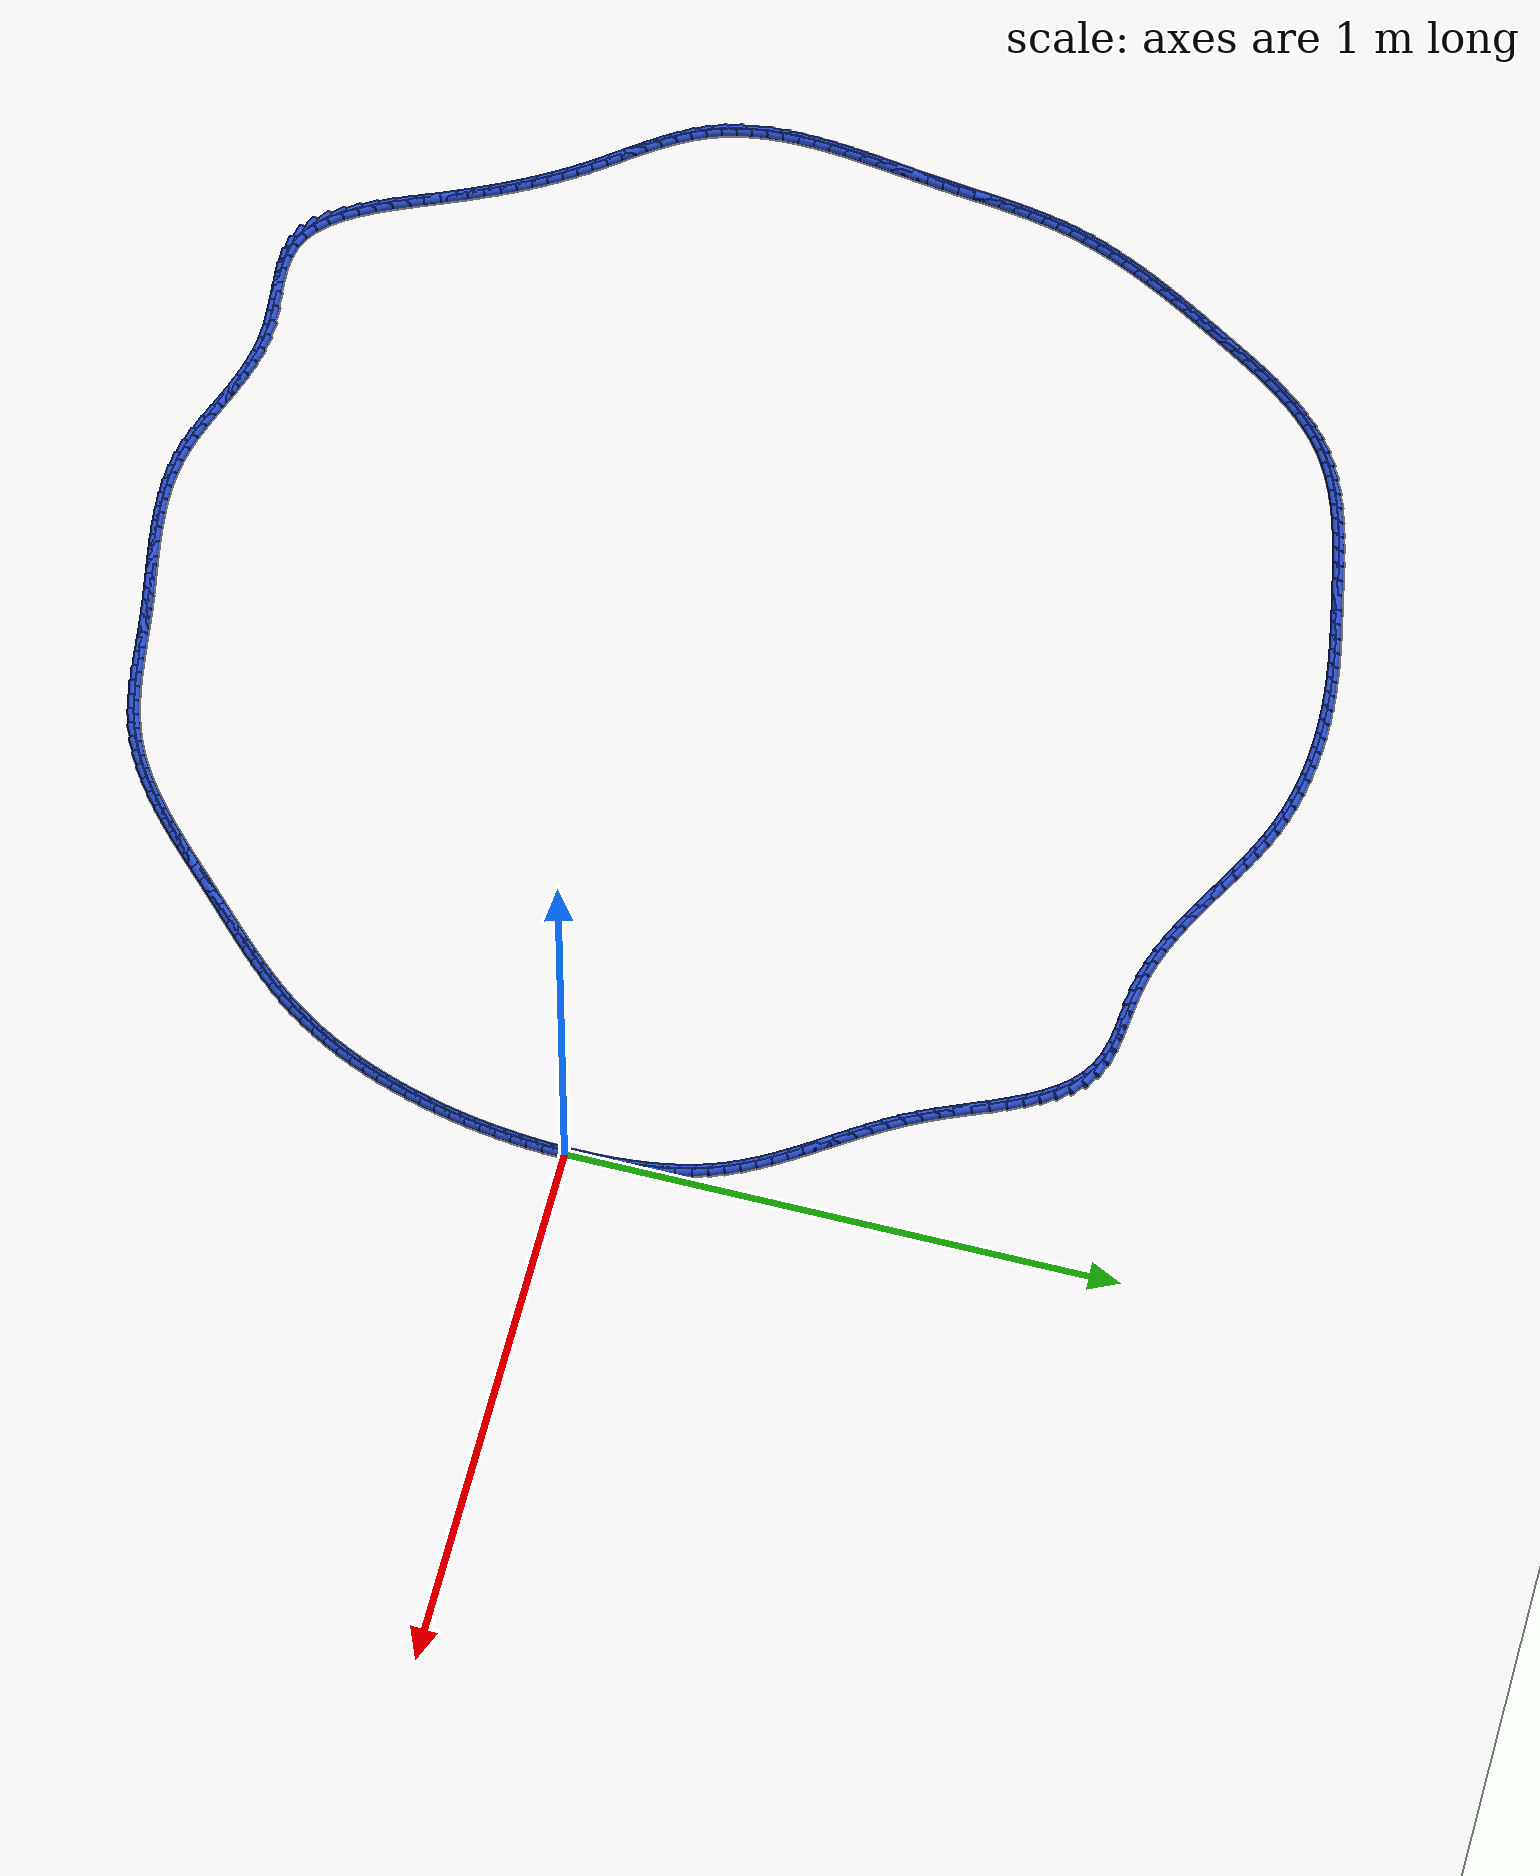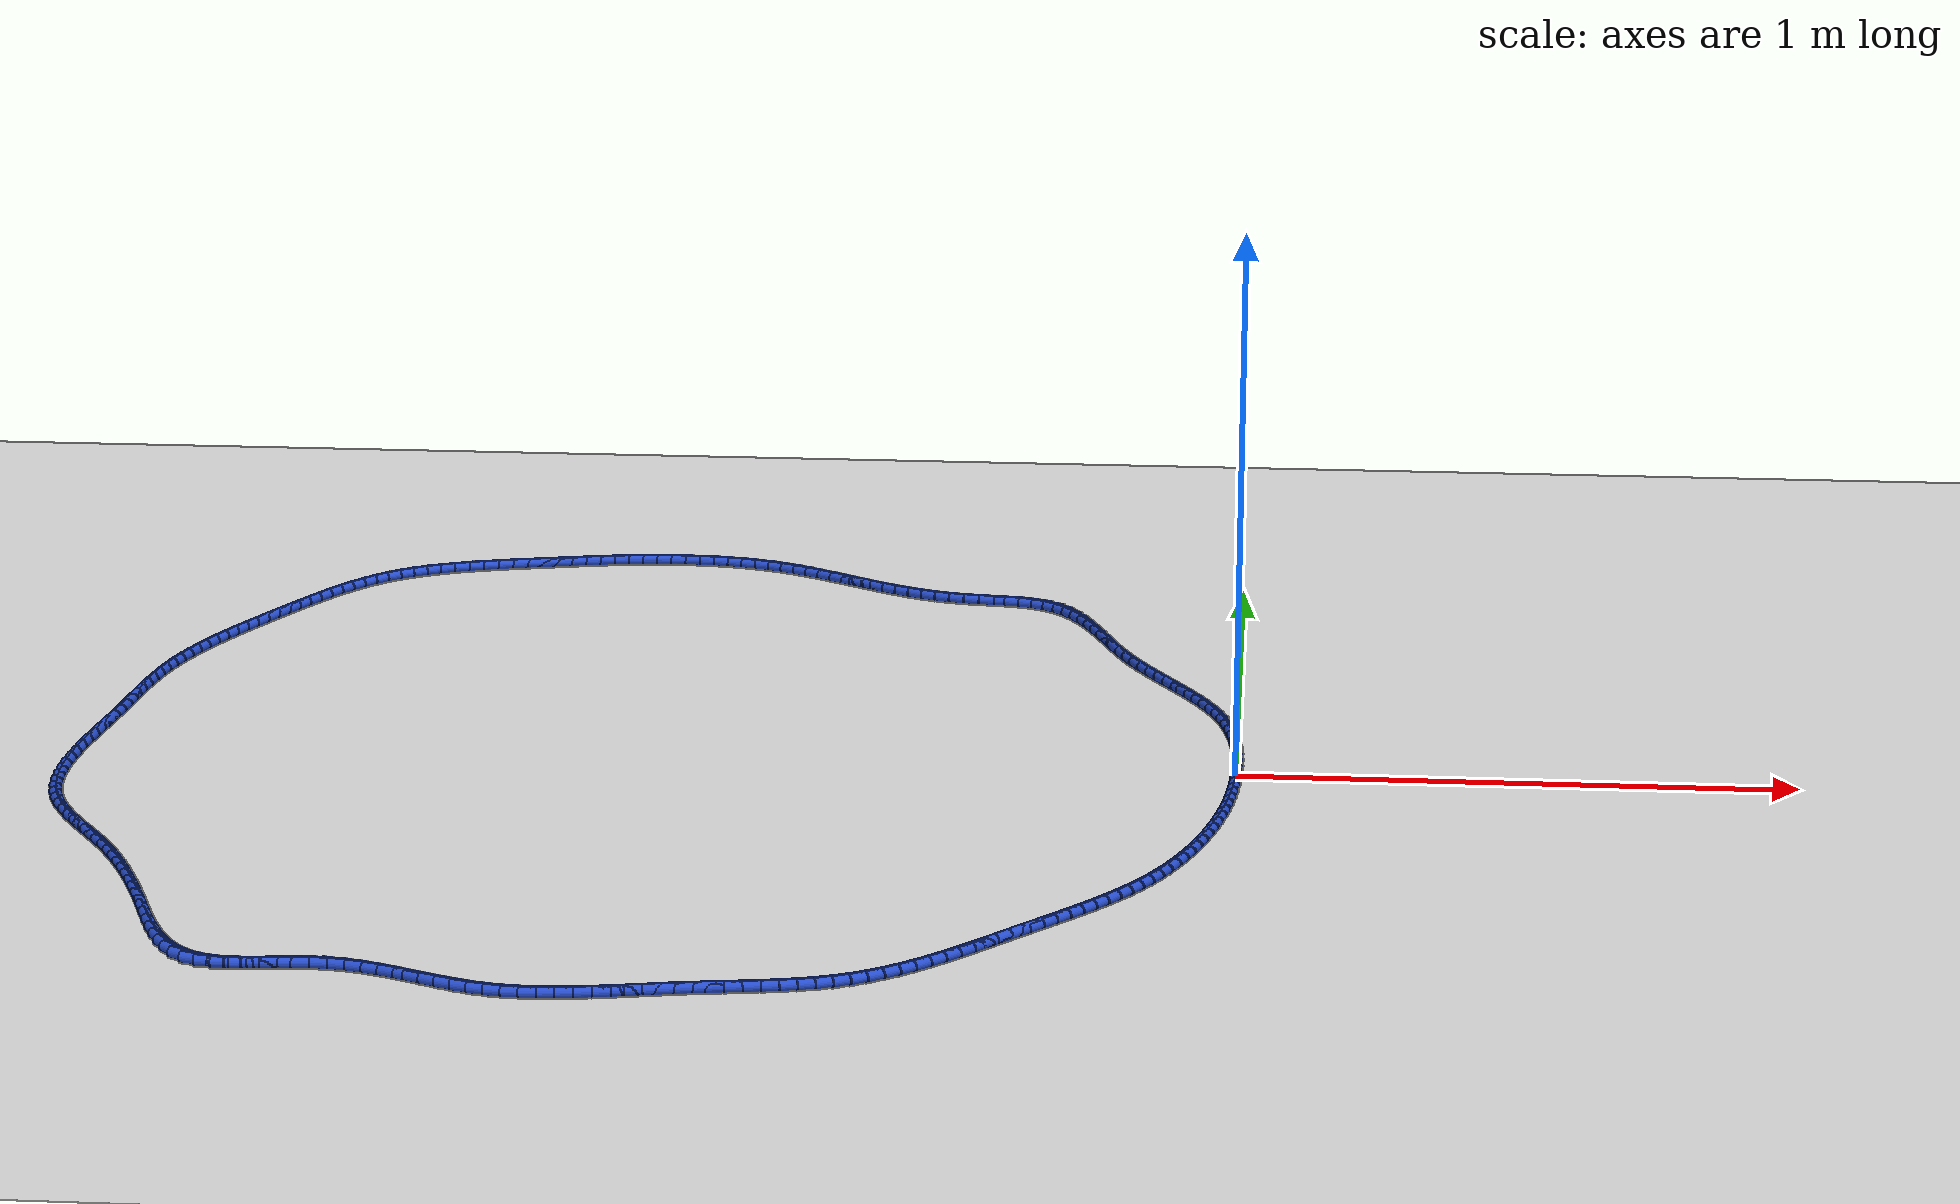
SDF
<sdf version="1.6">
 <world name="default">
  <light name="sun" type="directional">
   <pose>0 0 10 0 -0 0</pose>
   <diffuse>0.8 0.8 0.8 1</diffuse>
   <specular>0.2 0.2 0.2 1</specular>
   <attenuation>
    <range>1000</range>
    <constant>0.9</constant>
    <linear>0.01</linear>
    <quadratic>0.001</quadratic>
   </attenuation>
   <direction>-0.5 0.1 -0.9</direction>
  </light>
  <model name="ground_plane">
   <static>1</static>
   <link name="link">
    <collision name="collision">
     <geometry><plane><normal>0 0 1</normal><size>100 100</size></plane></geometry>
     <surface><friction><ode><mu>100</mu><mu2>50</mu2></ode></friction></surface>
    </collision>
    <visual name="visual">
     <cast_shadows>0</cast_shadows>
     <geometry><plane><normal>0 0 1</normal><size>100 100</size></plane></geometry>
     <material>
      <script><uri>file://media/materials/scripts/gazebo.material</uri><name>Gazebo/WhiteGlow</name></script>
     </material>
    </visual>
   </link>
  </model>
  <gravity>0 0 -9.8</gravity>
  <magnetic_field>6e-06 2.3e-05 -4.2e-05</magnetic_field>
  <atmosphere type="adiabatic"/>
  <physics name="default_physics" default="0" type="ode">
   <max_step_size>0.001</max_step_size>
   <real_time_factor>1</real_time_factor>
   <real_time_update_rate>1000</real_time_update_rate>
  </physics>
  <scene><ambient>0.4 0.4 0.4 1</ambient><background>0.7 0.7 0.7 1</background><shadows>1</shadows></scene>
  <spherical_coordinates>
   <surface_model>EARTH_WGS84</surface_model>
   <latitude_deg>0</latitude_deg>
   <longitude_deg>0</longitude_deg>
   <elevation>0</elevation>
   <heading_deg>0</heading_deg>
  </spherical_coordinates>
  <model name="line">
   <link name="link_0">
    <pose>3.469446951953614e-18 3.469446951953614e-17 0.01 0 1.57 1.5611416177436104</pose>
    <collision name="collision">
     <geometry><cylinder><radius>0.01</radius><length>0.08</length></cylinder></geometry>
    </collision>
    <visual name="visual">
     <material>
      <script><name>Gazebo/Blue</name><uri>file://media/materials/scripts/gazebo.material</uri></script>
     </material>
     <geometry><cylinder><radius>0.01</radius><length>0.08</length></cylinder></geometry>
    </visual>
   </link>
   <link name="link_1">
    <pose>0.0002862361532264347 0.029646388924655667 0.01 0 1.57 -1.5546341744531493</pose>
    <collision name="collision">
     <geometry><cylinder><radius>0.01</radius><length>0.08</length></cylinder></geometry>
    </collision>
    <visual name="visual">
     <material>
      <script><name>Gazebo/Blue</name><uri>file://media/materials/scripts/gazebo.material</uri></script>
     </material>
     <geometry><cylinder><radius>0.01</radius><length>0.08</length></cylinder></geometry>
    </visual>
   </link>
   <link name="link_2">
    <pose>-0.0001943225178980463 0.05937738125562229 0.01 0 1.57 -1.525424120462081</pose>
    <collision name="collision">
     <geometry><cylinder><radius>0.01</radius><length>0.08</length></cylinder></geometry>
    </collision>
    <visual name="visual">
     <material>
      <script><name>Gazebo/Blue</name><uri>file://media/materials/scripts/gazebo.material</uri></script>
     </material>
     <geometry><cylinder><radius>0.01</radius><length>0.08</length></cylinder></geometry>
    </visual>
   </link>
   <link name="link_3">
    <pose>-0.001542775128238215 0.08907677803118398 0.01 0 1.57 -1.492536186096775</pose>
    <collision name="collision">
     <geometry><cylinder><radius>0.01</radius><length>0.08</length></cylinder></geometry>
    </collision>
    <visual name="visual">
     <material>
      <script><name>Gazebo/Blue</name><uri>file://media/materials/scripts/gazebo.material</uri></script>
     </material>
     <geometry><cylinder><radius>0.01</radius><length>0.08</length></cylinder></geometry>
    </visual>
   </link>
   <link name="link_4">
    <pose>-0.0038602207926588467 0.11862838028962479 0.01 0 1.57 -1.4556434821974928</pose>
    <collision name="collision">
     <geometry><cylinder><radius>0.01</radius><length>0.08</length></cylinder></geometry>
    </collision>
    <visual name="visual">
     <material>
      <script><name>Gazebo/Blue</name><uri>file://media/materials/scripts/gazebo.material</uri></script>
     </material>
     <geometry><cylinder><radius>0.01</radius><length>0.08</length></cylinder></geometry>
    </visual>
   </link>
   <link name="link_5">
    <pose>-0.007247758626024722 0.14791598906922881 0.01 0 1.57 -1.4143834577324519</pose>
    <collision name="collision">
     <geometry><cylinder><radius>0.01</radius><length>0.08</length></cylinder></geometry>
    </collision>
    <visual name="visual">
     <material>
      <script><name>Gazebo/Blue</name><uri>file://media/materials/scripts/gazebo.material</uri></script>
     </material>
     <geometry><cylinder><radius>0.01</radius><length>0.08</length></cylinder></geometry>
    </visual>
   </link>
   <link name="link_6">
    <pose>-0.011806487743200611 0.17682340540827998 0.01 0 1.57 -1.3683694209193837</pose>
    <collision name="collision">
     <geometry><cylinder><radius>0.01</radius><length>0.08</length></cylinder></geometry>
    </collision>
    <visual name="visual">
     <material>
      <script><name>Gazebo/Blue</name><uri>file://media/materials/scripts/gazebo.material</uri></script>
     </material>
     <geometry><cylinder><radius>0.01</radius><length>0.08</length></cylinder></geometry>
    </visual>
   </link>
   <link name="link_7">
    <pose>-0.017637507259051298 0.2052344303450625 0.01 0 1.57 -1.3172096204345358</pose>
    <collision name="collision">
     <geometry><cylinder><radius>0.01</radius><length>0.08</length></cylinder></geometry>
    </collision>
    <visual name="visual">
     <material>
      <script><name>Gazebo/Blue</name><uri>file://media/materials/scripts/gazebo.material</uri></script>
     </material>
     <geometry><cylinder><radius>0.01</radius><length>0.08</length></cylinder></geometry>
    </visual>
   </link>
   <link name="link_8">
    <pose>-0.02484191628844155 0.2330328649178603 0.01 0 1.57 -1.2605368359717921</pose>
    <collision name="collision">
     <geometry><cylinder><radius>0.01</radius><length>0.08</length></cylinder></geometry>
    </collision>
    <visual name="visual">
     <material>
      <script><name>Gazebo/Blue</name><uri>file://media/materials/scripts/gazebo.material</uri></script>
     </material>
     <geometry><cylinder><radius>0.01</radius><length>0.08</length></cylinder></geometry>
    </visual>
   </link>
   <link name="link_9">
    <pose>-0.033520813946236155 0.26010251016495745 0.01 0 1.57 -1.1986327549780607</pose>
    <collision name="collision">
     <geometry><cylinder><radius>0.01</radius><length>0.08</length></cylinder></geometry>
    </collision>
    <visual name="visual">
     <material>
      <script><name>Gazebo/Blue</name><uri>file://media/materials/scripts/gazebo.material</uri></script>
     </material>
     <geometry><cylinder><radius>0.01</radius><length>0.08</length></cylinder></geometry>
    </visual>
   </link>
   <link name="link_10">
    <pose>-0.043762321679934484 0.28633895087391464 0.01 0 1.57 -1.139213759895514</pose>
    <collision name="collision">
     <geometry><cylinder><radius>0.01</radius><length>0.08</length></cylinder></geometry>
    </collision>
    <visual name="visual">
     <material>
      <script><name>Gazebo/Blue</name><uri>file://media/materials/scripts/gazebo.material</uri></script>
     </material>
     <geometry><cylinder><radius>0.01</radius><length>0.08</length></cylinder></geometry>
    </visual>
   </link>
   <link name="link_11">
    <pose>-0.055484500389116 0.311792187167663 0.01 0 1.57 -1.0884135133434998</pose>
    <collision name="collision">
     <geometry><cylinder><radius>0.01</radius><length>0.08</length></cylinder></geometry>
    </collision>
    <visual name="visual">
     <material>
      <script><name>Gazebo/Blue</name><uri>file://media/materials/scripts/gazebo.material</uri></script>
     </material>
     <geometry><cylinder><radius>0.01</radius><length>0.08</length></cylinder></geometry>
    </visual>
   </link>
   <link name="link_12">
    <pose>-0.06848583367064764 0.33662079561162334 0.01 0 1.57 -1.046906645319212</pose>
    <collision name="collision">
     <geometry><cylinder><radius>0.01</radius><length>0.08</length></cylinder></geometry>
    </collision>
    <visual name="visual">
     <material>
      <script><name>Gazebo/Blue</name><uri>file://media/materials/scripts/gazebo.material</uri></script>
     </material>
     <geometry><cylinder><radius>0.01</radius><length>0.08</length></cylinder></geometry>
    </visual>
   </link>
   <link name="link_13">
    <pose>-0.08256231834114076 0.3609856107729212 0.01 0 1.57 -1.0149220393269758</pose>
    <collision name="collision">
     <geometry><cylinder><radius>0.01</radius><length>0.08</length></cylinder></geometry>
    </collision>
    <visual name="visual">
     <material>
      <script><name>Gazebo/Blue</name><uri>file://media/materials/scripts/gazebo.material</uri></script>
     </material>
     <geometry><cylinder><radius>0.01</radius><length>0.08</length></cylinder></geometry>
    </visual>
   </link>
   <link name="link_14">
    <pose>-0.09750995121720682 0.38504746721868244 0.01 0 1.57 -0.9924559427208953</pose>
    <collision name="collision">
     <geometry><cylinder><radius>0.01</radius><length>0.08</length></cylinder></geometry>
    </collision>
    <visual name="visual">
     <material>
      <script><name>Gazebo/Blue</name><uri>file://media/materials/scripts/gazebo.material</uri></script>
     </material>
     <geometry><cylinder><radius>0.01</radius><length>0.08</length></cylinder></geometry>
    </visual>
   </link>
   <link name="link_15">
    <pose>-0.11312472911545718 0.4089671995160327 0.01 0 1.57 -0.9793613064949989</pose>
    <collision name="collision">
     <geometry><cylinder><radius>0.01</radius><length>0.08</length></cylinder></geometry>
    </collision>
    <visual name="visual">
     <material>
      <script><name>Gazebo/Blue</name><uri>file://media/materials/scripts/gazebo.material</uri></script>
     </material>
     <geometry><cylinder><radius>0.01</radius><length>0.08</length></cylinder></geometry>
    </visual>
   </link>
   <link name="link_16">
    <pose>-0.12920264885250338 0.43290564223209793 0.01 0 1.57 -0.9754129761379993</pose>
    <collision name="collision">
     <geometry><cylinder><radius>0.01</radius><length>0.08</length></cylinder></geometry>
    </collision>
    <visual name="visual">
     <material>
      <script><name>Gazebo/Blue</name><uri>file://media/materials/scripts/gazebo.material</uri></script>
     </material>
     <geometry><cylinder><radius>0.01</radius><length>0.08</length></cylinder></geometry>
    </visual>
   </link>
   <link name="link_17">
    <pose>-0.14553970724495666 0.4570236299340035 0.01 0 1.57 -0.9803460234140288</pose>
    <collision name="collision">
     <geometry><cylinder><radius>0.01</radius><length>0.08</length></cylinder></geometry>
    </collision>
    <visual name="visual">
     <material>
      <script><name>Gazebo/Blue</name><uri>file://media/materials/scripts/gazebo.material</uri></script>
     </material>
     <geometry><cylinder><radius>0.01</radius><length>0.08</length></cylinder></geometry>
    </visual>
   </link>
   <link name="link_18">
    <pose>-0.16193190110942854 0.4814819971888754 0.01 0 1.57 -0.9938693184062853</pose>
    <collision name="collision">
     <geometry><cylinder><radius>0.01</radius><length>0.08</length></cylinder></geometry>
    </collision>
    <visual name="visual">
     <material>
      <script><name>Gazebo/Blue</name><uri>file://media/materials/scripts/gazebo.material</uri></script>
     </material>
     <geometry><cylinder><radius>0.01</radius><length>0.08</length></cylinder></geometry>
    </visual>
   </link>
   <link name="link_19">
    <pose>-0.17817522726253038 0.5064415785638394 0.01 0 1.57 -1.0156583921871414</pose>
    <collision name="collision">
     <geometry><cylinder><radius>0.01</radius><length>0.08</length></cylinder></geometry>
    </collision>
    <visual name="visual">
     <material>
      <script><name>Gazebo/Blue</name><uri>file://media/materials/scripts/gazebo.material</uri></script>
     </material>
     <geometry><cylinder><radius>0.01</radius><length>0.08</length></cylinder></geometry>
    </visual>
   </link>
   <link name="link_20">
    <pose>-0.19406568252087364 0.5320632086260211 0.01 0 1.57 -1.0453324196126066</pose>
    <collision name="collision">
     <geometry><cylinder><radius>0.01</radius><length>0.08</length></cylinder></geometry>
    </collision>
    <visual name="visual">
     <material>
      <script><name>Gazebo/Blue</name><uri>file://media/materials/scripts/gazebo.material</uri></script>
     </material>
     <geometry><cylinder><radius>0.01</radius><length>0.08</length></cylinder></geometry>
    </visual>
   </link>
   <link name="link_21">
    <pose>-0.2093992637010697 0.5585077219425463 0.01 0 1.57 -1.082420973195867</pose>
    <collision name="collision">
     <geometry><cylinder><radius>0.01</radius><length>0.08</length></cylinder></geometry>
    </collision>
    <visual name="visual">
     <material>
      <script><name>Gazebo/Blue</name><uri>file://media/materials/scripts/gazebo.material</uri></script>
     </material>
     <geometry><cylinder><radius>0.01</radius><length>0.08</length></cylinder></geometry>
    </visual>
   </link>
   <link name="link_22">
    <pose>-0.22397196761973004 0.5859359530805407 0.01 0 1.57 -1.1229950869026593</pose>
    <collision name="collision">
     <geometry><cylinder><radius>0.01</radius><length>0.08</length></cylinder></geometry>
    </collision>
    <visual name="visual">
     <material>
      <script><name>Gazebo/Blue</name><uri>file://media/materials/scripts/gazebo.material</uri></script>
     </material>
     <geometry><cylinder><radius>0.01</radius><length>0.08</length></cylinder></geometry>
    </visual>
   </link>
   <link name="link_23">
    <pose>-0.23765443529940614 0.6144205546130449 0.01 0 1.57 -1.151316150730696</pose>
    <collision name="collision">
     <geometry><cylinder><radius>0.01</radius><length>0.08</length></cylinder></geometry>
    </collision>
    <visual name="visual">
     <material>
      <script><name>Gazebo/Blue</name><uri>file://media/materials/scripts/gazebo.material</uri></script>
     </material>
     <geometry><cylinder><radius>0.01</radius><length>0.08</length></cylinder></geometry>
    </visual>
   </link>
   <link name="link_24">
    <pose>-0.250673143220566 0.6436138078351127 0.01 0 1.57 -1.1637567197288379</pose>
    <collision name="collision">
     <geometry><cylinder><radius>0.01</radius><length>0.08</length></cylinder></geometry>
    </collision>
    <visual name="visual">
     <material>
      <script><name>Gazebo/Blue</name><uri>file://media/materials/scripts/gazebo.material</uri></script>
     </material>
     <geometry><cylinder><radius>0.01</radius><length>0.08</length></cylinder></geometry>
    </visual>
   </link>
   <link name="link_25">
    <pose>-0.26336048458814004 0.6730428678132798 0.01 0 1.57 -1.1607781366515253</pose>
    <collision name="collision">
     <geometry><cylinder><radius>0.01</radius><length>0.08</length></cylinder></geometry>
    </collision>
    <visual name="visual">
     <material>
      <script><name>Gazebo/Blue</name><uri>file://media/materials/scripts/gazebo.material</uri></script>
     </material>
     <geometry><cylinder><radius>0.01</radius><length>0.08</length></cylinder></geometry>
    </visual>
   </link>
   <link name="link_26">
    <pose>-0.2760488703823667 0.7022348686149683 0.01 0 1.57 -1.1419757918669842</pose>
    <collision name="collision">
     <geometry><cylinder><radius>0.01</radius><length>0.08</length></cylinder></geometry>
    </collision>
    <visual name="visual">
     <material>
      <script><name>Gazebo/Blue</name><uri>file://media/materials/scripts/gazebo.material</uri></script>
     </material>
     <geometry><cylinder><radius>0.01</radius><length>0.08</length></cylinder></geometry>
    </visual>
   </link>
   <link name="link_27">
    <pose>-0.2890707115834842 0.7307169443076011 0.01 0 1.57 -1.106033845268915</pose>
    <collision name="collision">
     <geometry><cylinder><radius>0.01</radius><length>0.08</length></cylinder></geometry>
    </collision>
    <visual name="visual">
     <material>
      <script><name>Gazebo/Blue</name><uri>file://media/materials/scripts/gazebo.material</uri></script>
     </material>
     <geometry><cylinder><radius>0.01</radius><length>0.08</length></cylinder></geometry>
    </visual>
   </link>
   <link name="link_28">
    <pose>-0.30275841917173074 0.7580162289586009 0.01 0 1.57 -1.0506958177985353</pose>
    <collision name="collision">
     <geometry><cylinder><radius>0.01</radius><length>0.08</length></cylinder></geometry>
    </collision>
    <visual name="visual">
     <material>
      <script><name>Gazebo/Blue</name><uri>file://media/materials/scripts/gazebo.material</uri></script>
     </material>
     <geometry><cylinder><radius>0.01</radius><length>0.08</length></cylinder></geometry>
    </visual>
   </link>
   <link name="link_29">
    <pose>-0.31744440412734454 0.7836598566353897 0.01 0 1.57 -0.9728523108346533</pose>
    <collision name="collision">
     <geometry><cylinder><radius>0.01</radius><length>0.08</length></cylinder></geometry>
    </collision>
    <visual name="visual">
     <material>
      <script><name>Gazebo/Blue</name><uri>file://media/materials/scripts/gazebo.material</uri></script>
     </material>
     <geometry><cylinder><radius>0.01</radius><length>0.08</length></cylinder></geometry>
    </visual>
   </link>
   <link name="link_30">
    <pose>-0.3334610774305641 0.807174961405391 0.01 0 1.57 -0.8689979100409678</pose>
    <collision name="collision">
     <geometry><cylinder><radius>0.01</radius><length>0.08</length></cylinder></geometry>
    </collision>
    <visual name="visual">
     <material>
      <script><name>Gazebo/Blue</name><uri>file://media/materials/scripts/gazebo.material</uri></script>
     </material>
     <geometry><cylinder><radius>0.01</radius><length>0.08</length></cylinder></geometry>
    </visual>
   </link>
   <link name="link_31">
    <pose>-0.35114085006162743 0.8280886773360269 0.01 0 1.57 -0.7365011632348717</pose>
    <collision name="collision">
     <geometry><cylinder><radius>0.01</radius><length>0.08</length></cylinder></geometry>
    </collision>
    <visual name="visual">
     <material>
      <script><name>Gazebo/Blue</name><uri>file://media/materials/scripts/gazebo.material</uri></script>
     </material>
     <geometry><cylinder><radius>0.01</radius><length>0.08</length></cylinder></geometry>
    </visual>
   </link>
   <link name="link_32">
    <pose>-0.37081613300077276 0.8459281384947198 0.01 0 1.57 -0.5760638978303527</pose>
    <collision name="collision">
     <geometry><cylinder><radius>0.01</radius><length>0.08</length></cylinder></geometry>
    </collision>
    <visual name="visual">
     <material>
      <script><name>Gazebo/Blue</name><uri>file://media/materials/scripts/gazebo.material</uri></script>
     </material>
     <geometry><cylinder><radius>0.01</radius><length>0.08</length></cylinder></geometry>
    </visual>
   </link>
   <link name="link_33">
    <pose>-0.39281933722823864 0.8602204789488929 0.01 0 1.57 -0.398183584581117</pose>
    <collision name="collision">
     <geometry><cylinder><radius>0.01</radius><length>0.08</length></cylinder></geometry>
    </collision>
    <visual name="visual">
     <material>
      <script><name>Gazebo/Blue</name><uri>file://media/materials/scripts/gazebo.material</uri></script>
     </material>
     <geometry><cylinder><radius>0.01</radius><length>0.08</length></cylinder></geometry>
    </visual>
   </link>
   <link name="link_34">
    <pose>-0.41743250955311484 0.8705741022432197 0.01 0 1.57 -0.2515774450017671</pose>
    <collision name="collision">
     <geometry><cylinder><radius>0.01</radius><length>0.08</length></cylinder></geometry>
    </collision>
    <visual name="visual">
     <material>
      <script><name>Gazebo/Blue</name><uri>file://media/materials/scripts/gazebo.material</uri></script>
     </material>
     <geometry><cylinder><radius>0.01</radius><length>0.08</length></cylinder></geometry>
    </visual>
   </link>
   <link name="link_35">
    <pose>-0.4443784538831552 0.8774998268179623 0.01 0 1.57 -0.15820959590631928</pose>
    <collision name="collision">
     <geometry><cylinder><radius>0.01</radius><length>0.08</length></cylinder></geometry>
    </collision>
    <visual name="visual">
     <material>
      <script><name>Gazebo/Blue</name><uri>file://media/materials/scripts/gazebo.material</uri></script>
     </material>
     <geometry><cylinder><radius>0.01</radius><length>0.08</length></cylinder></geometry>
    </visual>
   </link>
   <link name="link_36">
    <pose>-0.4730312536851178 0.8820711792310877 0.01 0 1.57 -0.11052053345426072</pose>
    <collision name="collision">
     <geometry><cylinder><radius>0.01</radius><length>0.08</length></cylinder></geometry>
    </collision>
    <visual name="visual">
     <material>
      <script><name>Gazebo/Blue</name><uri>file://media/materials/scripts/gazebo.material</uri></script>
     </material>
     <geometry><cylinder><radius>0.01</radius><length>0.08</length></cylinder></geometry>
    </visual>
   </link>
   <link name="link_37">
    <pose>-0.5027596998715201 0.8853702263005647 0.01 0 1.57 -0.10267090377072248</pose>
    <collision name="collision">
     <geometry><cylinder><radius>0.01</radius><length>0.08</length></cylinder></geometry>
    </collision>
    <visual name="visual">
     <material>
      <script><name>Gazebo/Blue</name><uri>file://media/materials/scripts/gazebo.material</uri></script>
     </material>
     <geometry><cylinder><radius>0.01</radius><length>0.08</length></cylinder></geometry>
    </visual>
   </link>
   <link name="link_38">
    <pose>-0.5329325833548804 0.8884790348443625 0.01 0 1.57 -0.132633073866147</pose>
    <collision name="collision">
     <geometry><cylinder><radius>0.01</radius><length>0.08</length></cylinder></geometry>
    </collision>
    <visual name="visual">
     <material>
      <script><name>Gazebo/Blue</name><uri>file://media/materials/scripts/gazebo.material</uri></script>
     </material>
     <geometry><cylinder><radius>0.01</radius><length>0.08</length></cylinder></geometry>
    </visual>
   </link>
   <link name="link_39">
    <pose>-0.562918695047717 0.8924796716804503 0.01 0 1.57 -0.19741876478757558</pose>
    <collision name="collision">
     <geometry><cylinder><radius>0.01</radius><length>0.08</length></cylinder></geometry>
    </collision>
    <visual name="visual">
     <material>
      <script><name>Gazebo/Blue</name><uri>file://media/materials/scripts/gazebo.material</uri></script>
     </material>
     <geometry><cylinder><radius>0.01</radius><length>0.08</length></cylinder></geometry>
    </visual>
   </link>
   <link name="link_40">
    <pose>-0.5921563687883306 0.8983279120285812 0.01 0 1.57 -0.2677372783503881</pose>
    <collision name="collision">
     <geometry><cylinder><radius>0.01</radius><length>0.08</length></cylinder></geometry>
    </collision>
    <visual name="visual">
     <material>
      <script><name>Gazebo/Blue</name><uri>file://media/materials/scripts/gazebo.material</uri></script>
     </material>
     <geometry><cylinder><radius>0.01</radius><length>0.08</length></cylinder></geometry>
    </visual>
   </link>
   <link name="link_41">
    <pose>-0.6205577482249681 0.9061190812859766 0.01 0 1.57 -0.3297167541286263</pose>
    <collision name="collision">
     <geometry><cylinder><radius>0.01</radius><length>0.08</length></cylinder></geometry>
    </collision>
    <visual name="visual">
     <material>
      <script><name>Gazebo/Blue</name><uri>file://media/materials/scripts/gazebo.material</uri></script>
     </material>
     <geometry><cylinder><radius>0.01</radius><length>0.08</length></cylinder></geometry>
    </visual>
   </link>
   <link name="link_42">
    <pose>-0.648232585267635 0.915589643572206 0.01 0 1.57 -0.3824720242395838</pose>
    <collision name="collision">
     <geometry><cylinder><radius>0.01</radius><length>0.08</length></cylinder></geometry>
    </collision>
    <visual name="visual">
     <material>
      <script><name>Gazebo/Blue</name><uri>file://media/materials/scripts/gazebo.material</uri></script>
     </material>
     <geometry><cylinder><radius>0.01</radius><length>0.08</length></cylinder></geometry>
    </visual>
   </link>
   <link name="link_43">
    <pose>-0.6752912880754629 0.9264748712429024 0.01 0 1.57 -0.4255542360717503</pose>
    <collision name="collision">
     <geometry><cylinder><radius>0.01</radius><length>0.08</length></cylinder></geometry>
    </collision>
    <visual name="visual">
     <material>
      <script><name>Gazebo/Blue</name><uri>file://media/materials/scripts/gazebo.material</uri></script>
     </material>
     <geometry><cylinder><radius>0.01</radius><length>0.08</length></cylinder></geometry>
    </visual>
   </link>
   <link name="link_44">
    <pose>-0.7018442648075837 0.9385100366536999 0.01 0 1.57 -0.45878975750319156</pose>
    <collision name="collision">
     <geometry><cylinder><radius>0.01</radius><length>0.08</length></cylinder></geometry>
    </collision>
    <visual name="visual">
     <material>
      <script><name>Gazebo/Blue</name><uri>file://media/materials/scripts/gazebo.material</uri></script>
     </material>
     <geometry><cylinder><radius>0.01</radius><length>0.08</length></cylinder></geometry>
    </visual>
   </link>
   <link name="link_45">
    <pose>-0.7280019236231287 0.9514304121602307 0.01 0 1.57 -0.4821634026316077</pose>
    <collision name="collision">
     <geometry><cylinder><radius>0.01</radius><length>0.08</length></cylinder></geometry>
    </collision>
    <visual name="visual">
     <material>
      <script><name>Gazebo/Blue</name><uri>file://media/materials/scripts/gazebo.material</uri></script>
     </material>
     <geometry><cylinder><radius>0.01</radius><length>0.08</length></cylinder></geometry>
    </visual>
   </link>
   <link name="link_46">
    <pose>-0.7538746726812298 0.9649712701181287 0.01 0 1.57 -0.49572235111081114</pose>
    <collision name="collision">
     <geometry><cylinder><radius>0.01</radius><length>0.08</length></cylinder></geometry>
    </collision>
    <visual name="visual">
     <material>
      <script><name>Gazebo/Blue</name><uri>file://media/materials/scripts/gazebo.material</uri></script>
     </material>
     <geometry><cylinder><radius>0.01</radius><length>0.08</length></cylinder></geometry>
    </visual>
   </link>
   <link name="link_47">
    <pose>-0.7795729201410186 0.9788678828830268 0.01 0 1.57 -0.49950828175360495</pose>
    <collision name="collision">
     <geometry><cylinder><radius>0.01</radius><length>0.08</length></cylinder></geometry>
    </collision>
    <visual name="visual">
     <material>
      <script><name>Gazebo/Blue</name><uri>file://media/materials/scripts/gazebo.material</uri></script>
     </material>
     <geometry><cylinder><radius>0.01</radius><length>0.08</length></cylinder></geometry>
    </visual>
   </link>
   <link name="link_48">
    <pose>-0.8052070741616271 0.9928555228105586 0.01 0 1.57 -0.4935184887555524</pose>
    <collision name="collision">
     <geometry><cylinder><radius>0.01</radius><length>0.08</length></cylinder></geometry>
    </collision>
    <visual name="visual">
     <material>
      <script><name>Gazebo/Blue</name><uri>file://media/materials/scripts/gazebo.material</uri></script>
     </material>
     <geometry><cylinder><radius>0.01</radius><length>0.08</length></cylinder></geometry>
    </visual>
   </link>
   <link name="link_49">
    <pose>-0.8308875429021867 1.006669462256357 0.01 0 1.57 -0.47769484025326275</pose>
    <collision name="collision">
     <geometry><cylinder><radius>0.01</radius><length>0.08</length></cylinder></geometry>
    </collision>
    <visual name="visual">
     <material>
      <script><name>Gazebo/Blue</name><uri>file://media/materials/scripts/gazebo.material</uri></script>
     </material>
     <geometry><cylinder><radius>0.01</radius><length>0.08</length></cylinder></geometry>
    </visual>
   </link>
   <link name="link_50">
    <pose>-0.8567247345218288 1.0200449735760553 0.01 0 1.57 -0.45194037814710103</pose>
    <collision name="collision">
     <geometry><cylinder><radius>0.01</radius><length>0.08</length></cylinder></geometry>
    </collision>
    <visual name="visual">
     <material>
      <script><name>Gazebo/Blue</name><uri>file://media/materials/scripts/gazebo.material</uri></script>
     </material>
     <geometry><cylinder><radius>0.01</radius><length>0.08</length></cylinder></geometry>
    </visual>
   </link>
   <link name="link_51">
    <pose>-0.8828290571796858 1.032717329125287 0.01 0 1.57 -0.416165105256358</pose>
    <collision name="collision">
     <geometry><cylinder><radius>0.01</radius><length>0.08</length></cylinder></geometry>
    </collision>
    <visual name="visual">
     <material>
      <script><name>Gazebo/Blue</name><uri>file://media/materials/scripts/gazebo.material</uri></script>
     </material>
     <geometry><cylinder><radius>0.01</radius><length>0.08</length></cylinder></geometry>
    </visual>
   </link>
   <link name="link_52">
    <pose>-0.9093109190348889 1.0444218012596846 0.01 0 1.57 -0.37036303819420036</pose>
    <collision name="collision">
     <geometry><cylinder><radius>0.01</radius><length>0.08</length></cylinder></geometry>
    </collision>
    <visual name="visual">
     <material>
      <script><name>Gazebo/Blue</name><uri>file://media/materials/scripts/gazebo.material</uri></script>
     </material>
     <geometry><cylinder><radius>0.01</radius><length>0.08</length></cylinder></geometry>
    </visual>
   </link>
   <link name="link_53">
    <pose>-0.9362807282465697 1.0548936623348824 0.01 0 1.57 -0.315485280029026</pose>
    <collision name="collision">
     <geometry><cylinder><radius>0.01</radius><length>0.08</length></cylinder></geometry>
    </collision>
    <visual name="visual">
     <material>
      <script><name>Gazebo/Blue</name><uri>file://media/materials/scripts/gazebo.material</uri></script>
     </material>
     <geometry><cylinder><radius>0.01</radius><length>0.08</length></cylinder></geometry>
    </visual>
   </link>
   <link name="link_54">
    <pose>-0.9638365308373273 1.063887499743705 0.01 0 1.57 -0.2595835985764379</pose>
    <collision name="collision">
     <geometry><cylinder><radius>0.01</radius><length>0.08</length></cylinder></geometry>
    </collision>
    <visual name="visual">
     <material>
      <script><name>Gazebo/Blue</name><uri>file://media/materials/scripts/gazebo.material</uri></script>
     </material>
     <geometry><cylinder><radius>0.01</radius><length>0.08</length></cylinder></geometry>
    </visual>
   </link>
   <link name="link_55">
    <pose>-0.9919508728730868 1.07135398642812 0.01 0 1.57 -0.20711975091673546</pose>
    <collision name="collision">
     <geometry><cylinder><radius>0.01</radius><length>0.08</length></cylinder></geometry>
    </collision>
    <visual name="visual">
     <material>
      <script><name>Gazebo/Blue</name><uri>file://media/materials/scripts/gazebo.material</uri></script>
     </material>
     <geometry><cylinder><radius>0.01</radius><length>0.08</length></cylinder></geometry>
    </visual>
   </link>
   <link name="link_56">
    <pose>-1.0205232166164269 1.0773579840365548 0.01 0 1.57 -0.15795295898424394</pose>
    <collision name="collision">
     <geometry><cylinder><radius>0.01</radius><length>0.08</length></cylinder></geometry>
    </collision>
    <visual name="visual">
     <material>
      <script><name>Gazebo/Blue</name><uri>file://media/materials/scripts/gazebo.material</uri></script>
     </material>
     <geometry><cylinder><radius>0.01</radius><length>0.08</length></cylinder></geometry>
    </visual>
   </link>
   <link name="link_57">
    <pose>-1.0494521160689276 1.0819657733163826 0.01 0 1.57 -0.1118482912921753</pose>
    <collision name="collision">
     <geometry><cylinder><radius>0.01</radius><length>0.08</length></cylinder></geometry>
    </collision>
    <visual name="visual">
     <material>
      <script><name>Gazebo/Blue</name><uri>file://media/materials/scripts/gazebo.material</uri></script>
     </material>
     <geometry><cylinder><radius>0.01</radius><length>0.08</length></cylinder></geometry>
    </visual>
   </link>
   <link name="link_58">
    <pose>-1.0786361252321695 1.0852436350149781 0.01 0 1.57 -0.06854868838956527</pose>
    <collision name="collision">
     <geometry><cylinder><radius>0.01</radius><length>0.08</length></cylinder></geometry>
    </collision>
    <visual name="visual">
     <material>
      <script><name>Gazebo/Blue</name><uri>file://media/materials/scripts/gazebo.material</uri></script>
     </material>
     <geometry><cylinder><radius>0.01</radius><length>0.08</length></cylinder></geometry>
    </visual>
   </link>
   <link name="link_59">
    <pose>-1.1079737981077338 1.0872578498797152 0.01 0 1.57 -0.027786375727203612</pose>
    <collision name="collision">
     <geometry><cylinder><radius>0.01</radius><length>0.08</length></cylinder></geometry>
    </collision>
    <visual name="visual">
     <material>
      <script><name>Gazebo/Blue</name><uri>file://media/materials/scripts/gazebo.material</uri></script>
     </material>
     <geometry><cylinder><radius>0.01</radius><length>0.08</length></cylinder></geometry>
    </visual>
   </link>
   <link name="link_60">
    <pose>-1.1373636886971998 1.0880746986579672 0.01 0 1.57 0.010709524680330476</pose>
    <collision name="collision">
     <geometry><cylinder><radius>0.01</radius><length>0.08</length></cylinder></geometry>
    </collision>
    <visual name="visual">
     <material>
      <script><name>Gazebo/Blue</name><uri>file://media/materials/scripts/gazebo.material</uri></script>
     </material>
     <geometry><cylinder><radius>0.01</radius><length>0.08</length></cylinder></geometry>
    </visual>
   </link>
   <link name="link_61">
    <pose>-1.1667043510021489 1.087760462097109 0.01 0 1.57 0.047208533782803604</pose>
    <collision name="collision">
     <geometry><cylinder><radius>0.01</radius><length>0.08</length></cylinder></geometry>
    </collision>
    <visual name="visual">
     <material>
      <script><name>Gazebo/Blue</name><uri>file://media/materials/scripts/gazebo.material</uri></script>
     </material>
     <geometry><cylinder><radius>0.01</radius><length>0.08</length></cylinder></geometry>
    </visual>
   </link>
   <link name="link_62">
    <pose>-1.1958943390241608 1.0863814209445146 0.01 0 1.57 0.08170957465477997</pose>
    <collision name="collision">
     <geometry><cylinder><radius>0.01</radius><length>0.08</length></cylinder></geometry>
    </collision>
    <visual name="visual">
     <material>
      <script><name>Gazebo/Blue</name><uri>file://media/materials/scripts/gazebo.material</uri></script>
     </material>
     <geometry><cylinder><radius>0.01</radius><length>0.08</length></cylinder></geometry>
    </visual>
   </link>
   <link name="link_63">
    <pose>-1.224850785462752 1.0840101223830483 0.01 0 1.57 0.11268024942012114</pose>
    <collision name="collision">
     <geometry><cylinder><radius>0.01</radius><length>0.08</length></cylinder></geometry>
    </collision>
    <visual name="visual">
     <material>
      <script><name>Gazebo/Blue</name><uri>file://media/materials/scripts/gazebo.material</uri></script>
     </material>
     <geometry><cylinder><radius>0.01</radius><length>0.08</length></cylinder></geometry>
    </visual>
   </link>
   <link name="link_64">
    <pose>-1.2536020764411715 1.0807566384213396 0.01 0 1.57 0.1392839832924681</pose>
    <collision name="collision">
     <geometry><cylinder><radius>0.01</radius><length>0.08</length></cylinder></geometry>
    </collision>
    <visual name="visual">
     <material>
      <script><name>Gazebo/Blue</name><uri>file://media/materials/scripts/gazebo.material</uri></script>
     </material>
     <geometry><cylinder><radius>0.01</radius><length>0.08</length></cylinder></geometry>
    </visual>
   </link>
   <link name="link_65">
    <pose>-1.2822178260492196 1.0767449469075832 0.01 0 1.57 0.16131512518770366</pose>
    <collision name="collision">
     <geometry><cylinder><radius>0.01</radius><length>0.08</length></cylinder></geometry>
    </collision>
    <visual name="visual">
     <material>
      <script><name>Gazebo/Blue</name><uri>file://media/materials/scripts/gazebo.material</uri></script>
     </material>
     <geometry><cylinder><radius>0.01</radius><length>0.08</length></cylinder></geometry>
    </visual>
   </link>
   <link name="link_66">
    <pose>-1.3107677156888409 1.0720990483937807 0.01 0 1.57 0.1786504673311753</pose>
    <collision name="collision">
     <geometry><cylinder><radius>0.01</radius><length>0.08</length></cylinder></geometry>
    </collision>
    <visual name="visual">
     <material>
      <script><name>Gazebo/Blue</name><uri>file://media/materials/scripts/gazebo.material</uri></script>
     </material>
     <geometry><cylinder><radius>0.01</radius><length>0.08</length></cylinder></geometry>
    </visual>
   </link>
   <link name="link_67">
    <pose>-1.3393214267619808 1.0669429434319362 0.01 0 1.57 0.19123697754447946</pose>
    <collision name="collision">
     <geometry><cylinder><radius>0.01</radius><length>0.08</length></cylinder></geometry>
    </collision>
    <visual name="visual">
     <material>
      <script><name>Gazebo/Blue</name><uri>file://media/materials/scripts/gazebo.material</uri></script>
     </material>
     <geometry><cylinder><radius>0.01</radius><length>0.08</length></cylinder></geometry>
    </visual>
   </link>
   <link name="link_68">
    <pose>-1.3679486406705839 1.0614006325740521 0.01 0 1.57 0.19908063609595766</pose>
    <collision name="collision">
     <geometry><cylinder><radius>0.01</radius><length>0.08</length></cylinder></geometry>
    </collision>
    <visual name="visual">
     <material>
      <script><name>Gazebo/Blue</name><uri>file://media/materials/scripts/gazebo.material</uri></script>
     </material>
     <geometry><cylinder><radius>0.01</radius><length>0.08</length></cylinder></geometry>
    </visual>
   </link>
   <link name="link_69">
    <pose>-1.3967190388165946 1.0555961163721317 0.01 0 1.57 0.20225039987977708</pose>
    <collision name="collision">
     <geometry><cylinder><radius>0.01</radius><length>0.08</length></cylinder></geometry>
    </collision>
    <visual name="visual">
     <material>
      <script><name>Gazebo/Blue</name><uri>file://media/materials/scripts/gazebo.material</uri></script>
     </material>
     <geometry><cylinder><radius>0.01</radius><length>0.08</length></cylinder></geometry>
    </visual>
   </link>
   <link name="link_70">
    <pose>-1.4257020323311904 1.049653038182516 0.01 0 1.57 0.20409639836431703</pose>
    <collision name="collision">
     <geometry><cylinder><radius>0.01</radius><length>0.08</length></cylinder></geometry>
    </collision>
    <visual name="visual">
     <material>
      <script><name>Gazebo/Blue</name><uri>file://media/materials/scripts/gazebo.material</uri></script>
     </material>
     <geometry><cylinder><radius>0.01</radius><length>0.08</length></cylinder></geometry>
    </visual>
   </link>
   <link name="link_71">
    <pose>-1.4549021206749815 1.0436092527012355 0.01 0 1.57 0.2120882974977242</pose>
    <collision name="collision">
     <geometry><cylinder><radius>0.01</radius><length>0.08</length></cylinder></geometry>
    </collision>
    <visual name="visual">
     <material>
      <script><name>Gazebo/Blue</name><uri>file://media/materials/scripts/gazebo.material</uri></script>
     </material>
     <geometry><cylinder><radius>0.01</radius><length>0.08</length></cylinder></geometry>
    </visual>
   </link>
   <link name="link_72">
    <pose>-1.484175045874034 1.0373060135985033 0.01 0 1.57 0.22728179407487384</pose>
    <collision name="collision">
     <geometry><cylinder><radius>0.01</radius><length>0.08</length></cylinder></geometry>
    </collision>
    <visual name="visual">
     <material>
      <script><name>Gazebo/Blue</name><uri>file://media/materials/scripts/gazebo.material</uri></script>
     </material>
     <geometry><cylinder><radius>0.01</radius><length>0.08</length></cylinder></geometry>
    </visual>
   </link>
   <link name="link_73">
    <pose>-1.5133557984365718 1.030557148892111 0.01 0 1.57 0.24984621767397297</pose>
    <collision name="collision">
     <geometry><cylinder><radius>0.01</radius><length>0.08</length></cylinder></geometry>
    </collision>
    <visual name="visual">
     <material>
      <script><name>Gazebo/Blue</name><uri>file://media/materials/scripts/gazebo.material</uri></script>
     </material>
     <geometry><cylinder><radius>0.01</radius><length>0.08</length></cylinder></geometry>
    </visual>
   </link>
   <link name="link_74">
    <pose>-1.54227936887082 1.0231764865998505 0.01 0 1.57 0.28009517804462747</pose>
    <collision name="collision">
     <geometry><cylinder><radius>0.01</radius><length>0.08</length></cylinder></geometry>
    </collision>
    <visual name="visual">
     <material>
      <script><name>Gazebo/Blue</name><uri>file://media/materials/scripts/gazebo.material</uri></script>
     </material>
     <geometry><cylinder><radius>0.01</radius><length>0.08</length></cylinder></geometry>
    </visual>
   </link>
   <link name="link_75">
    <pose>-1.5707807476850024 1.0149778547395132 0.01 0 1.57 0.3184598409877497</pose>
    <collision name="collision">
     <geometry><cylinder><radius>0.01</radius><length>0.08</length></cylinder></geometry>
    </collision>
    <visual name="visual">
     <material>
      <script><name>Gazebo/Blue</name><uri>file://media/materials/scripts/gazebo.material</uri></script>
     </material>
     <geometry><cylinder><radius>0.01</radius><length>0.08</length></cylinder></geometry>
    </visual>
   </link>
   <link name="link_76">
    <pose>-1.5986949253873435 1.005775081328891 0.01 0 1.57 0.36544647114574463</pose>
    <collision name="collision">
     <geometry><cylinder><radius>0.01</radius><length>0.08</length></cylinder></geometry>
    </collision>
    <visual name="visual">
     <material>
      <script><name>Gazebo/Blue</name><uri>file://media/materials/scripts/gazebo.material</uri></script>
     </material>
     <geometry><cylinder><radius>0.01</radius><length>0.08</length></cylinder></geometry>
    </visual>
   </link>
   <link name="link_77">
    <pose>-1.6258568924860675 0.9953819943857752 0.01 0 1.57 0.42156786668374135</pose>
    <collision name="collision">
     <geometry><cylinder><radius>0.01</radius><length>0.08</length></cylinder></geometry>
    </collision>
    <visual name="visual">
     <material>
      <script><name>Gazebo/Blue</name><uri>file://media/materials/scripts/gazebo.material</uri></script>
     </material>
     <geometry><cylinder><radius>0.01</radius><length>0.08</length></cylinder></geometry>
    </visual>
   </link>
   <link name="link_78">
    <pose>-1.6521016394893986 0.9836124219279577 0.01 0 1.57 0.48723743629992217</pose>
    <collision name="collision">
     <geometry><cylinder><radius>0.01</radius><length>0.08</length></cylinder></geometry>
    </collision>
    <visual name="visual">
     <material>
      <script><name>Gazebo/Blue</name><uri>file://media/materials/scripts/gazebo.material</uri></script>
     </material>
     <geometry><cylinder><radius>0.01</radius><length>0.08</length></cylinder></geometry>
    </visual>
   </link>
   <link name="link_79">
    <pose>-1.677264156905562 0.9702801919732298 0.01 0 1.57 0.5626186906064433</pose>
    <collision name="collision">
     <geometry><cylinder><radius>0.01</radius><length>0.08</length></cylinder></geometry>
    </collision>
    <visual name="visual">
     <material>
      <script><name>Gazebo/Blue</name><uri>file://media/materials/scripts/gazebo.material</uri></script>
     </material>
     <geometry><cylinder><radius>0.01</radius><length>0.08</length></cylinder></geometry>
    </visual>
   </link>
   <link name="link_80">
    <pose>-1.7011794352427811 0.9551991325393837 0.01 0 1.57 0.6462365374783721</pose>
    <collision name="collision">
     <geometry><cylinder><radius>0.01</radius><length>0.08</length></cylinder></geometry>
    </collision>
    <visual name="visual">
     <material>
      <script><name>Gazebo/Blue</name><uri>file://media/materials/scripts/gazebo.material</uri></script>
     </material>
     <geometry><cylinder><radius>0.01</radius><length>0.08</length></cylinder></geometry>
    </visual>
   </link>
   <link name="link_81">
    <pose>-1.7237030596637308 0.9382099476870462 0.01 0 1.57 0.7265328022150184</pose>
    <collision name="collision">
     <geometry><cylinder><radius>0.01</radius><length>0.08</length></cylinder></geometry>
    </collision>
    <visual name="visual">
     <material>
      <script><name>Gazebo/Blue</name><uri>file://media/materials/scripts/gazebo.material</uri></script>
     </material>
     <geometry><cylinder><radius>0.01</radius><length>0.08</length></cylinder></geometry>
    </visual>
   </link>
   <link name="link_82">
    <pose>-1.7448752884058611 0.9193943400078116 0.01 0 1.57 0.7971487204633396</pose>
    <collision name="collision">
     <geometry><cylinder><radius>0.01</radius><length>0.08</length></cylinder></geometry>
    </collision>
    <visual name="visual">
     <material>
      <script><name>Gazebo/Blue</name><uri>file://media/materials/scripts/gazebo.material</uri></script>
     </material>
     <geometry><cylinder><radius>0.01</radius><length>0.08</length></cylinder></geometry>
    </visual>
   </link>
   <link name="link_83">
    <pose>-1.7648338155804875 0.8989611659975081 0.01 0 1.57 0.857889771509862</pose>
    <collision name="collision">
     <geometry><cylinder><radius>0.01</radius><length>0.08</length></cylinder></geometry>
    </collision>
    <visual name="visual">
     <material>
      <script><name>Gazebo/Blue</name><uri>file://media/materials/scripts/gazebo.material</uri></script>
     </material>
     <geometry><cylinder><radius>0.01</radius><length>0.08</length></cylinder></geometry>
    </visual>
   </link>
   <link name="link_84">
    <pose>-1.783717213352504 0.877120428012689 0.01 0 1.57 0.908991931478706</pose>
    <collision name="collision">
     <geometry><cylinder><radius>0.01</radius><length>0.08</length></cylinder></geometry>
    </collision>
    <visual name="visual">
     <material>
      <script><name>Gazebo/Blue</name><uri>file://media/materials/scripts/gazebo.material</uri></script>
     </material>
     <geometry><cylinder><radius>0.01</radius><length>0.08</length></cylinder></geometry>
    </visual>
   </link>
   <link name="link_85">
    <pose>-1.8016640538868087 0.8540821284099069 0.01 0 1.57 0.950890666696185</pose>
    <collision name="collision">
     <geometry><cylinder><radius>0.01</radius><length>0.08</length></cylinder></geometry>
    </collision>
    <visual name="visual">
     <material>
      <script><name>Gazebo/Blue</name><uri>file://media/materials/scripts/gazebo.material</uri></script>
     </material>
     <geometry><cylinder><radius>0.01</radius><length>0.08</length></cylinder></geometry>
    </visual>
   </link>
   <link name="link_86">
    <pose>-1.8188129093482956 0.830056269545715 0.01 0 1.57 0.9840834608351404</pose>
    <collision name="collision">
     <geometry><cylinder><radius>0.01</radius><length>0.08</length></cylinder></geometry>
    </collision>
    <visual name="visual">
     <material>
      <script><name>Gazebo/Blue</name><uri>file://media/materials/scripts/gazebo.material</uri></script>
     </material>
     <geometry><cylinder><radius>0.01</radius><length>0.08</length></cylinder></geometry>
    </visual>
   </link>
   <link name="link_87">
    <pose>-1.8353023519018627 0.8052528537766673 0.01 0 1.57 1.0090360288794324</pose>
    <collision name="collision">
     <geometry><cylinder><radius>0.01</radius><length>0.08</length></cylinder></geometry>
    </collision>
    <visual name="visual">
     <material>
      <script><name>Gazebo/Blue</name><uri>file://media/materials/scripts/gazebo.material</uri></script>
     </material>
     <geometry><cylinder><radius>0.01</radius><length>0.08</length></cylinder></geometry>
    </visual>
   </link>
   <link name="link_88">
    <pose>-1.8512709537124055 0.779881883459316 0.01 0 1.57 1.0261231932457995</pose>
    <collision name="collision">
     <geometry><cylinder><radius>0.01</radius><length>0.08</length></cylinder></geometry>
    </collision>
    <visual name="visual">
     <material>
      <script><name>Gazebo/Blue</name><uri>file://media/materials/scripts/gazebo.material</uri></script>
     </material>
     <geometry><cylinder><radius>0.01</radius><length>0.08</length></cylinder></geometry>
    </visual>
   </link>
   <link name="link_89">
    <pose>-1.8668572869448194 0.7541533609502145 0.01 0 1.57 1.0355934250239995</pose>
    <collision name="collision">
     <geometry><cylinder><radius>0.01</radius><length>0.08</length></cylinder></geometry>
    </collision>
    <visual name="visual">
     <material>
      <script><name>Gazebo/Blue</name><uri>file://media/materials/scripts/gazebo.material</uri></script>
     </material>
     <geometry><cylinder><radius>0.01</radius><length>0.08</length></cylinder></geometry>
    </visual>
   </link>
   <link name="link_90">
    <pose>-1.8821999225502963 0.7282772873263528 0.01 0 1.57 1.0394956941263556</pose>
    <collision name="collision">
     <geometry><cylinder><radius>0.01</radius><length>0.08</length></cylinder></geometry>
    </collision>
    <visual name="visual">
     <material>
      <script><name>Gazebo/Blue</name><uri>file://media/materials/scripts/gazebo.material</uri></script>
     </material>
     <geometry><cylinder><radius>0.01</radius><length>0.08</length></cylinder></geometry>
    </visual>
   </link>
   <link name="link_91">
    <pose>-1.8973956092796758 0.7024195721187517 0.01 0 1.57 1.0449305170318683</pose>
    <collision name="collision">
     <geometry><cylinder><radius>0.01</radius><length>0.08</length></cylinder></geometry>
    </collision>
    <visual name="visual">
     <material>
      <script><name>Gazebo/Blue</name><uri>file://media/materials/scripts/gazebo.material</uri></script>
     </material>
     <geometry><cylinder><radius>0.01</radius><length>0.08</length></cylinder></geometry>
    </visual>
   </link>
   <link name="link_92">
    <pose>-1.9123889683830682 0.676585742653872 0.01 0 1.57 1.0535525621790696</pose>
    <collision name="collision">
     <geometry><cylinder><radius>0.01</radius><length>0.08</length></cylinder></geometry>
    </collision>
    <visual name="visual">
     <material>
      <script><name>Gazebo/Blue</name><uri>file://media/materials/scripts/gazebo.material</uri></script>
     </material>
     <geometry><cylinder><radius>0.01</radius><length>0.08</length></cylinder></geometry>
    </visual>
   </link>
   <link name="link_93">
    <pose>-1.9270900416886432 0.65074487049642 0.01 0 1.57 1.0654211243568747</pose>
    <collision name="collision">
     <geometry><cylinder><radius>0.01</radius><length>0.08</length></cylinder></geometry>
    </collision>
    <visual name="visual">
     <material>
      <script><name>Gazebo/Blue</name><uri>file://media/materials/scripts/gazebo.material</uri></script>
     </material>
     <geometry><cylinder><radius>0.01</radius><length>0.08</length></cylinder></geometry>
    </visual>
   </link>
   <link name="link_94">
    <pose>-1.9414088710245716 0.6248660272111016 0.01 0 1.57 1.080604065194326</pose>
    <collision name="collision">
     <geometry><cylinder><radius>0.01</radius><length>0.08</length></cylinder></geometry>
    </collision>
    <visual name="visual">
     <material>
      <script><name>Gazebo/Blue</name><uri>file://media/materials/scripts/gazebo.material</uri></script>
     </material>
     <geometry><cylinder><radius>0.01</radius><length>0.08</length></cylinder></geometry>
    </visual>
   </link>
   <link name="link_95">
    <pose>-1.9552554982190231 0.5989182843626237 0.01 0 1.57 1.0991744904192882</pose>
    <collision name="collision">
     <geometry><cylinder><radius>0.01</radius><length>0.08</length></cylinder></geometry>
    </collision>
    <visual name="visual">
     <material>
      <script><name>Gazebo/Blue</name><uri>file://media/materials/scripts/gazebo.material</uri></script>
     </material>
     <geometry><cylinder><radius>0.01</radius><length>0.08</length></cylinder></geometry>
    </visual>
   </link>
   <link name="link_96">
    <pose>-1.9685399651001692 0.5728707135156921 0.01 0 1.57 1.1212060238936634</pose>
    <collision name="collision">
     <geometry><cylinder><radius>0.01</radius><length>0.08</length></cylinder></geometry>
    </collision>
    <visual name="visual">
     <material>
      <script><name>Gazebo/Blue</name><uri>file://media/materials/scripts/gazebo.material</uri></script>
     </material>
     <geometry><cylinder><radius>0.01</radius><length>0.08</length></cylinder></geometry>
    </visual>
   </link>
   <link name="link_97">
    <pose>-1.9811723134961796 0.5466923862350136 0.01 0 1.57 1.1467664616136561</pose>
    <collision name="collision">
     <geometry><cylinder><radius>0.01</radius><length>0.08</length></cylinder></geometry>
    </collision>
    <visual name="visual">
     <material>
      <script><name>Gazebo/Blue</name><uri>file://media/materials/scripts/gazebo.material</uri></script>
     </material>
     <geometry><cylinder><radius>0.01</radius><length>0.08</length></cylinder></geometry>
    </visual>
   </link>
   <link name="link_98">
    <pose>-1.9930625852352253 0.5203523740852943 0.01 0 1.57 1.1759096296076628</pose>
    <collision name="collision">
     <geometry><cylinder><radius>0.01</radius><length>0.08</length></cylinder></geometry>
    </collision>
    <visual name="visual">
     <material>
      <script><name>Gazebo/Blue</name><uri>file://media/materials/scripts/gazebo.material</uri></script>
     </material>
     <geometry><cylinder><radius>0.01</radius><length>0.08</length></cylinder></geometry>
    </visual>
   </link>
   <link name="link_99">
    <pose>-2.0041208221454756 0.49381974863123973 0.01 0 1.57 1.208665380438519</pose>
    <collision name="collision">
     <geometry><cylinder><radius>0.01</radius><length>0.08</length></cylinder></geometry>
    </collision>
    <visual name="visual">
     <material>
      <script><name>Gazebo/Blue</name><uri>file://media/materials/scripts/gazebo.material</uri></script>
     </material>
     <geometry><cylinder><radius>0.01</radius><length>0.08</length></cylinder></geometry>
    </visual>
   </link>
   <link name="link_100">
    <pose>-2.0142570660551025 0.46706358143755744 0.01 0 1.57 1.2450278693126124</pose>
    <collision name="collision">
     <geometry><cylinder><radius>0.01</radius><length>0.08</length></cylinder></geometry>
    </collision>
    <visual name="visual">
     <material>
      <script><name>Gazebo/Blue</name><uri>file://media/materials/scripts/gazebo.material</uri></script>
     </material>
     <geometry><cylinder><radius>0.01</radius><length>0.08</length></cylinder></geometry>
    </visual>
   </link>
   <link name="link_101">
    <pose>-2.0233813587922755 0.4400529440689525 0.01 0 1.57 1.284942570876051</pose>
    <collision name="collision">
     <geometry><cylinder><radius>0.01</radius><length>0.08</length></cylinder></geometry>
    </collision>
    <visual name="visual">
     <material>
      <script><name>Gazebo/Blue</name><uri>file://media/materials/scripts/gazebo.material</uri></script>
     </material>
     <geometry><cylinder><radius>0.01</radius><length>0.08</length></cylinder></geometry>
    </visual>
   </link>
   <link name="link_102">
    <pose>-2.031403742185165 0.4127569080901323 0.01 0 1.57 1.3271658144277942</pose>
    <collision name="collision">
     <geometry><cylinder><radius>0.01</radius><length>0.08</length></cylinder></geometry>
    </collision>
    <visual name="visual">
     <material>
      <script><name>Gazebo/Blue</name><uri>file://media/materials/scripts/gazebo.material</uri></script>
     </material>
     <geometry><cylinder><radius>0.01</radius><length>0.08</length></cylinder></geometry>
    </visual>
   </link>
   <link name="link_103">
    <pose>-2.038265984201959 0.38514981449354085 0.01 0 1.57 1.365330983333939</pose>
    <collision name="collision">
     <geometry><cylinder><radius>0.01</radius><length>0.08</length></cylinder></geometry>
    </collision>
    <visual name="visual">
     <material>
      <script><name>Gazebo/Blue</name><uri>file://media/materials/scripts/gazebo.material</uri></script>
     </material>
     <geometry><cylinder><radius>0.01</radius><length>0.08</length></cylinder></geometry>
    </visual>
   </link>
   <link name="link_104">
    <pose>-2.044083635602141 0.3572348680369746 0.01 0 1.57 1.397168854580767</pose>
    <collision name="collision">
     <geometry><cylinder><radius>0.01</radius><length>0.08</length></cylinder></geometry>
    </collision>
    <visual name="visual">
     <material>
      <script><name>Gazebo/Blue</name><uri>file://media/materials/scripts/gazebo.material</uri></script>
     </material>
     <geometry><cylinder><radius>0.01</radius><length>0.08</length></cylinder></geometry>
    </visual>
   </link>
   <link name="link_105">
    <pose>-2.0490314452451335 0.32902510575248994 0.01 0 1.57 1.4226260404690254</pose>
    <collision name="collision">
     <geometry><cylinder><radius>0.01</radius><length>0.08</length></cylinder></geometry>
    </collision>
    <visual name="visual">
     <material>
      <script><name>Gazebo/Blue</name><uri>file://media/materials/scripts/gazebo.material</uri></script>
     </material>
     <geometry><cylinder><radius>0.01</radius><length>0.08</length></cylinder></geometry>
    </visual>
   </link>
   <link name="link_106">
    <pose>-2.0532842118261856 0.3005335729494286 0.01 0 1.57 1.4417371279195235</pose>
    <collision name="collision">
     <geometry><cylinder><radius>0.01</radius><length>0.08</length></cylinder></geometry>
    </collision>
    <visual name="visual">
     <material>
      <script><name>Gazebo/Blue</name><uri>file://media/materials/scripts/gazebo.material</uri></script>
     </material>
     <geometry><cylinder><radius>0.01</radius><length>0.08</length></cylinder></geometry>
    </visual>
   </link>
   <link name="link_107">
    <pose>-2.0570167340405487 0.271773314937132 0.01 0 1.57 1.454590649719538</pose>
    <collision name="collision">
     <geometry><cylinder><radius>0.01</radius><length>0.08</length></cylinder></geometry>
    </collision>
    <visual name="visual">
     <material>
      <script><name>Gazebo/Blue</name><uri>file://media/materials/scripts/gazebo.material</uri></script>
     </material>
     <geometry><cylinder><radius>0.01</radius><length>0.08</length></cylinder></geometry>
    </visual>
   </link>
   <link name="link_108">
    <pose>-2.0604038105834723 0.24275737702494118 0.01 0 1.57 1.4613047921438742</pose>
    <collision name="collision">
     <geometry><cylinder><radius>0.01</radius><length>0.08</length></cylinder></geometry>
    </collision>
    <visual name="visual">
     <material>
      <script><name>Gazebo/Blue</name><uri>file://media/materials/scripts/gazebo.material</uri></script>
     </material>
     <geometry><cylinder><radius>0.01</radius><length>0.08</length></cylinder></geometry>
    </visual>
   </link>
   <link name="link_109">
    <pose>-2.0636202401502066 0.21349880452219835 0.01 0 1.57 1.4620114188816438</pose>
    <collision name="collision">
     <geometry><cylinder><radius>0.01</radius><length>0.08</length></cylinder></geometry>
    </collision>
    <visual name="visual">
     <material>
      <script><name>Gazebo/Blue</name><uri>file://media/materials/scripts/gazebo.material</uri></script>
     </material>
     <geometry><cylinder><radius>0.01</radius><length>0.08</length></cylinder></geometry>
    </visual>
   </link>
   <link name="link_110">
    <pose>-2.0668408214360023 0.1840106427382442 0.01 0 1.57 1.4568478663190563</pose>
    <collision name="collision">
     <geometry><cylinder><radius>0.01</radius><length>0.08</length></cylinder></geometry>
    </collision>
    <visual name="visual">
     <material>
      <script><name>Gazebo/Blue</name><uri>file://media/materials/scripts/gazebo.material</uri></script>
     </material>
     <geometry><cylinder><radius>0.01</radius><length>0.08</length></cylinder></geometry>
    </visual>
   </link>
   <link name="link_111">
    <pose>-2.070240353136109 0.15430593698242095 0.01 0 1.57 1.446715431470572</pose>
    <collision name="collision">
     <geometry><cylinder><radius>0.01</radius><length>0.08</length></cylinder></geometry>
    </collision>
    <visual name="visual">
     <material>
      <script><name>Gazebo/Blue</name><uri>file://media/materials/scripts/gazebo.material</uri></script>
     </material>
     <geometry><cylinder><radius>0.01</radius><length>0.08</length></cylinder></geometry>
    </visual>
   </link>
   <link name="link_112">
    <pose>-2.0739701546148916 0.1244009272955888 0.01 0 1.57 1.4387756884809653</pose>
    <collision name="collision">
     <geometry><cylinder><radius>0.01</radius><length>0.08</length></cylinder></geometry>
    </collision>
    <visual name="visual">
     <material>
      <script><name>Gazebo/Blue</name><uri>file://media/materials/scripts/gazebo.material</uri></script>
     </material>
     <geometry><cylinder><radius>0.01</radius><length>0.08</length></cylinder></geometry>
    </visual>
   </link>
   <link name="link_113">
    <pose>-2.0779618037324137 0.09434175299953233 0.01 0 1.57 1.4367804453872022</pose>
    <collision name="collision">
     <geometry><cylinder><radius>0.01</radius><length>0.08</length></cylinder></geometry>
    </collision>
    <visual name="visual">
     <material>
      <script><name>Gazebo/Blue</name><uri>file://media/materials/scripts/gazebo.material</uri></script>
     </material>
     <geometry><cylinder><radius>0.01</radius><length>0.08</length></cylinder></geometry>
    </visual>
   </link>
   <link name="link_114">
    <pose>-2.0820268648346403 0.06419088313846738 0.01 0 1.57 1.4406927988133817</pose>
    <collision name="collision">
     <geometry><cylinder><radius>0.01</radius><length>0.08</length></cylinder></geometry>
    </collision>
    <visual name="visual">
     <material>
      <script><name>Gazebo/Blue</name><uri>file://media/materials/scripts/gazebo.material</uri></script>
     </material>
     <geometry><cylinder><radius>0.01</radius><length>0.08</length></cylinder></geometry>
    </visual>
   </link>
   <link name="link_115">
    <pose>-2.085975685970697 0.034010952252889456 0.01 0 1.57 1.4505379887904355</pose>
    <collision name="collision">
     <geometry><cylinder><radius>0.01</radius><length>0.08</length></cylinder></geometry>
    </collision>
    <visual name="visual">
     <material>
      <script><name>Gazebo/Blue</name><uri>file://media/materials/scripts/gazebo.material</uri></script>
     </material>
     <geometry><cylinder><radius>0.01</radius><length>0.08</length></cylinder></geometry>
    </visual>
   </link>
   <link name="link_116">
    <pose>-2.0896186151897047 0.0038645948832926767 0.01 0 1.57 1.4664390557508917</pose>
    <collision name="collision">
     <geometry><cylinder><radius>0.01</radius><length>0.08</length></cylinder></geometry>
    </collision>
    <visual name="visual">
     <material>
      <script><name>Gazebo/Blue</name><uri>file://media/materials/scripts/gazebo.material</uri></script>
     </material>
     <geometry><cylinder><radius>0.01</radius><length>0.08</length></cylinder></geometry>
    </visual>
   </link>
   <link name="link_117">
    <pose>-2.0927660005407884 -0.02618555442982909 0.01 0 1.57 1.4886104450520554</pose>
    <collision name="collision">
     <geometry><cylinder><radius>0.01</radius><length>0.08</length></cylinder></geometry>
    </collision>
    <visual name="visual">
     <material>
      <script><name>Gazebo/Blue</name><uri>file://media/materials/scripts/gazebo.material</uri></script>
     </material>
     <geometry><cylinder><radius>0.01</radius><length>0.08</length></cylinder></geometry>
    </visual>
   </link>
   <link name="link_118">
    <pose>-2.0952281900730694 -0.05607686114597964 0.01 0 1.57 1.5173470851522761</pose>
    <collision name="collision">
     <geometry><cylinder><radius>0.01</radius><length>0.08</length></cylinder></geometry>
    </collision>
    <visual name="visual">
     <material>
      <script><name>Gazebo/Blue</name><uri>file://media/materials/scripts/gazebo.material</uri></script>
     </material>
     <geometry><cylinder><radius>0.01</radius><length>0.08</length></cylinder></geometry>
    </visual>
   </link>
   <link name="link_119">
    <pose>-2.096815531835672 -0.08574669072466515 0.01 0 1.57 1.5530058177310029</pose>
    <collision name="collision">
     <geometry><cylinder><radius>0.01</radius><length>0.08</length></cylinder></geometry>
    </collision>
    <visual name="visual">
     <material>
      <script><name>Gazebo/Blue</name><uri>file://media/materials/scripts/gazebo.material</uri></script>
     </material>
     <geometry><cylinder><radius>0.01</radius><length>0.08</length></cylinder></geometry>
    </visual>
   </link>
   <link name="link_120">
    <pose>-2.0973383738777187 -0.11513240862539104 0.01 0 1.57 -1.545617918537367</pose>
    <collision name="collision">
     <geometry><cylinder><radius>0.01</radius><length>0.08</length></cylinder></geometry>
    </collision>
    <visual name="visual">
     <material>
      <script><name>Gazebo/Blue</name><uri>file://media/materials/scripts/gazebo.material</uri></script>
     </material>
     <geometry><cylinder><radius>0.01</radius><length>0.08</length></cylinder></geometry>
    </visual>
   </link>
   <link name="link_121">
    <pose>-2.096607064248332 -0.14417138030766263 0.01 0 1.57 -1.4949676953276398</pose>
    <collision name="collision">
     <geometry><cylinder><radius>0.01</radius><length>0.08</length></cylinder></geometry>
    </collision>
    <visual name="visual">
     <material>
      <script><name>Gazebo/Blue</name><uri>file://media/materials/scripts/gazebo.material</uri></script>
     </material>
     <geometry><cylinder><radius>0.01</radius><length>0.08</length></cylinder></geometry>
    </visual>
   </link>
   <link name="link_122">
    <pose>-2.094431950996636 -0.17280097123098612 0.01 0 1.57 -1.4363531281535007</pose>
    <collision name="collision">
     <geometry><cylinder><radius>0.01</radius><length>0.08</length></cylinder></geometry>
    </collision>
    <visual name="visual">
     <material>
      <script><name>Gazebo/Blue</name><uri>file://media/materials/scripts/gazebo.material</uri></script>
     </material>
     <geometry><cylinder><radius>0.01</radius><length>0.08</length></cylinder></geometry>
    </visual>
   </link>
   <link name="link_123">
    <pose>-2.090623382171753 -0.20095854685486536 0.01 0 1.57 -1.369675777400341</pose>
    <collision name="collision">
     <geometry><cylinder><radius>0.01</radius><length>0.08</length></cylinder></geometry>
    </collision>
    <visual name="visual">
     <material>
      <script><name>Gazebo/Blue</name><uri>file://media/materials/scripts/gazebo.material</uri></script>
     </material>
     <geometry><cylinder><radius>0.01</radius><length>0.08</length></cylinder></geometry>
    </visual>
   </link>
   <link name="link_124">
    <pose>-2.0849917058228056 -0.2285814726388064 0.01 0 1.57 -1.2951387918760018</pose>
    <collision name="collision">
     <geometry><cylinder><radius>0.01</radius><length>0.08</length></cylinder></geometry>
    </collision>
    <visual name="visual">
     <material>
      <script><name>Gazebo/Blue</name><uri>file://media/materials/scripts/gazebo.material</uri></script>
     </material>
     <geometry><cylinder><radius>0.01</radius><length>0.08</length></cylinder></geometry>
    </visual>
   </link>
   <link name="link_125">
    <pose>-2.077347269998918 -0.2556071140423148 0.01 0 1.57 -1.2133664070064372</pose>
    <collision name="collision">
     <geometry><cylinder><radius>0.01</radius><length>0.08</length></cylinder></geometry>
    </collision>
    <visual name="visual">
     <material>
      <script><name>Gazebo/Blue</name><uri>file://media/materials/scripts/gazebo.material</uri></script>
     </material>
     <geometry><cylinder><radius>0.01</radius><length>0.08</length></cylinder></geometry>
    </visual>
   </link>
   <link name="link_126">
    <pose>-2.0675004245700257 -0.2819728370286596 0.01 0 1.57 -1.129462282693284</pose>
    <collision name="collision">
     <geometry><cylinder><radius>0.01</radius><length>0.08</length></cylinder></geometry>
    </collision>
    <visual name="visual">
     <material>
      <script><name>Gazebo/Blue</name><uri>file://media/materials/scripts/gazebo.material</uri></script>
     </material>
     <geometry><cylinder><radius>0.01</radius><length>0.08</length></cylinder></geometry>
    </visual>
   </link>
   <link name="link_127">
    <pose>-2.055371877863093 -0.3076465403632765 0.01 0 1.57 -1.0589013907691092</pose>
    <collision name="collision">
     <geometry><cylinder><radius>0.01</radius><length>0.08</length></cylinder></geometry>
    </collision>
    <visual name="visual">
     <material>
      <script><name>Gazebo/Blue</name><uri>file://media/materials/scripts/gazebo.material</uri></script>
     </material>
     <geometry><cylinder><radius>0.01</radius><length>0.08</length></cylinder></geometry>
    </visual>
   </link>
   <link name="link_128">
    <pose>-2.0412905242066715 -0.3327090553658456 0.01 0 1.57 -1.0045620188056497</pose>
    <collision name="collision">
     <geometry><cylinder><radius>0.01</radius><length>0.08</length></cylinder></geometry>
    </collision>
    <visual name="visual">
     <material>
      <script><name>Gazebo/Blue</name><uri>file://media/materials/scripts/gazebo.material</uri></script>
     </material>
     <geometry><cylinder><radius>0.01</radius><length>0.08</length></cylinder></geometry>
    </visual>
   </link>
   <link name="link_129">
    <pose>-2.0256796097920207 -0.3572673176242267 0.01 0 1.57 -0.9655197287707613</pose>
    <collision name="collision">
     <geometry><cylinder><radius>0.01</radius><length>0.08</length></cylinder></geometry>
    </collision>
    <visual name="visual">
     <material>
      <script><name>Gazebo/Blue</name><uri>file://media/materials/scripts/gazebo.material</uri></script>
     </material>
     <geometry><cylinder><radius>0.01</radius><length>0.08</length></cylinder></geometry>
    </visual>
   </link>
   <link name="link_130">
    <pose>-2.008962380810401 -0.3814282627262802 0.01 0 1.57 -0.9409079899022532</pose>
    <collision name="collision">
     <geometry><cylinder><radius>0.01</radius><length>0.08</length></cylinder></geometry>
    </collision>
    <visual name="visual">
     <material>
      <script><name>Gazebo/Blue</name><uri>file://media/materials/scripts/gazebo.material</uri></script>
     </material>
     <geometry><cylinder><radius>0.01</radius><length>0.08</length></cylinder></geometry>
    </visual>
   </link>
   <link name="link_131">
    <pose>-1.9915620834530692 -0.40529882625986635 0.01 0 1.57 -0.9301441768434988</pose>
    <collision name="collision">
     <geometry><cylinder><radius>0.01</radius><length>0.08</length></cylinder></geometry>
    </collision>
    <visual name="visual">
     <material>
      <script><name>Gazebo/Blue</name><uri>file://media/materials/scripts/gazebo.material</uri></script>
     </material>
     <geometry><cylinder><radius>0.01</radius><length>0.08</length></cylinder></geometry>
    </visual>
   </link>
   <link name="link_132">
    <pose>-1.9739019639112867 -0.4289859438128441 0.01 0 1.57 -0.9330463618013296</pose>
    <collision name="collision">
     <geometry><cylinder><radius>0.01</radius><length>0.08</length></cylinder></geometry>
    </collision>
    <visual name="visual">
     <material>
      <script><name>Gazebo/Blue</name><uri>file://media/materials/scripts/gazebo.material</uri></script>
     </material>
     <geometry><cylinder><radius>0.01</radius><length>0.08</length></cylinder></geometry>
    </visual>
   </link>
   <link name="link_133">
    <pose>-1.9564052683763133 -0.45259655097307416 0.01 0 1.57 -0.9498866189387403</pose>
    <collision name="collision">
     <geometry><cylinder><radius>0.01</radius><length>0.08</length></cylinder></geometry>
    </collision>
    <visual name="visual">
     <material>
      <script><name>Gazebo/Blue</name><uri>file://media/materials/scripts/gazebo.material</uri></script>
     </material>
     <geometry><cylinder><radius>0.01</radius><length>0.08</length></cylinder></geometry>
    </visual>
   </link>
   <link name="link_134">
    <pose>-1.9394952339651494 -0.47623758311217235 0.01 0 1.57 -0.9783592508208356</pose>
    <collision name="collision">
     <geometry><cylinder><radius>0.01</radius><length>0.08</length></cylinder></geometry>
    </collision>
    <visual name="visual">
     <material>
      <script><name>Gazebo/Blue</name><uri>file://media/materials/scripts/gazebo.material</uri></script>
     </material>
     <geometry><cylinder><radius>0.01</radius><length>0.08</length></cylinder></geometry>
    </visual>
   </link>
   <link name="link_135">
    <pose>-1.923491866626553 -0.5000135155518068 0.01 0 1.57 -1.008261042093803</pose>
    <collision name="collision">
     <geometry><cylinder><radius>0.01</radius><length>0.08</length></cylinder></geometry>
    </collision>
    <visual name="visual">
     <material>
      <script><name>Gazebo/Blue</name><uri>file://media/materials/scripts/gazebo.material</uri></script>
     </material>
     <geometry><cylinder><radius>0.01</radius><length>0.08</length></cylinder></geometry>
    </visual>
   </link>
   <link name="link_136">
    <pose>-1.908355925110128 -0.5240202625746786 0.01 0 1.57 -1.0368419629974048</pose>
    <collision name="collision">
     <geometry><cylinder><radius>0.01</radius><length>0.08</length></cylinder></geometry>
    </collision>
    <visual name="visual">
     <material>
      <script><name>Gazebo/Blue</name><uri>file://media/materials/scripts/gazebo.material</uri></script>
     </material>
     <geometry><cylinder><radius>0.01</radius><length>0.08</length></cylinder></geometry>
    </visual>
   </link>
   <link name="link_137">
    <pose>-1.893970070330991 -0.5483518773533529 0.01 0 1.57 -1.0636110853884124</pose>
    <collision name="collision">
     <geometry><cylinder><radius>0.01</radius><length>0.08</length></cylinder></geometry>
    </collision>
    <visual name="visual">
     <material>
      <script><name>Gazebo/Blue</name><uri>file://media/materials/scripts/gazebo.material</uri></script>
     </material>
     <geometry><cylinder><radius>0.01</radius><length>0.08</length></cylinder></geometry>
    </visual>
   </link>
   <link name="link_138">
    <pose>-1.8802169632042574 -0.5731024130603949 0.01 0 1.57 -1.0881453965187684</pose>
    <collision name="collision">
     <geometry><cylinder><radius>0.01</radius><length>0.08</length></cylinder></geometry>
    </collision>
    <visual name="visual">
     <material>
      <script><name>Gazebo/Blue</name><uri>file://media/materials/scripts/gazebo.material</uri></script>
     </material>
     <geometry><cylinder><radius>0.01</radius><length>0.08</length></cylinder></geometry>
    </visual>
   </link>
   <link name="link_139">
    <pose>-1.8669792646450436 -0.5983659228683695 0.01 0 1.57 -1.1101105679967844</pose>
    <collision name="collision">
     <geometry><cylinder><radius>0.01</radius><length>0.08</length></cylinder></geometry>
    </collision>
    <visual name="visual">
     <material>
      <script><name>Gazebo/Blue</name><uri>file://media/materials/scripts/gazebo.material</uri></script>
     </material>
     <geometry><cylinder><radius>0.01</radius><length>0.08</length></cylinder></geometry>
    </visual>
   </link>
   <link name="link_140">
    <pose>-1.8541396355684652 -0.6242364599498419 0.01 0 1.57 -1.1292725497309861</pose>
    <collision name="collision">
     <geometry><cylinder><radius>0.01</radius><length>0.08</length></cylinder></geometry>
    </collision>
    <visual name="visual">
     <material>
      <script><name>Gazebo/Blue</name><uri>file://media/materials/scripts/gazebo.material</uri></script>
     </material>
     <geometry><cylinder><radius>0.01</radius><length>0.08</length></cylinder></geometry>
    </visual>
   </link>
   <link name="link_141">
    <pose>-1.8415807368896384 -0.6508080774773758 0.01 0 1.57 -1.1454998494109716</pose>
    <collision name="collision">
     <geometry><cylinder><radius>0.01</radius><length>0.08</length></cylinder></geometry>
    </collision>
    <visual name="visual">
     <material>
      <script><name>Gazebo/Blue</name><uri>file://media/materials/scripts/gazebo.material</uri></script>
     </material>
     <geometry><cylinder><radius>0.01</radius><length>0.08</length></cylinder></geometry>
    </visual>
   </link>
   <link name="link_142">
    <pose>-1.8291852295236797 -0.678174828623537 0.01 0 1.57 -1.1587577849653563</pose>
    <collision name="collision">
     <geometry><cylinder><radius>0.01</radius><length>0.08</length></cylinder></geometry>
    </collision>
    <visual name="visual">
     <material>
      <script><name>Gazebo/Blue</name><uri>file://media/materials/scripts/gazebo.material</uri></script>
     </material>
     <geometry><cylinder><radius>0.01</radius><length>0.08</length></cylinder></geometry>
    </visual>
   </link>
   <link name="link_143">
    <pose>-1.8168357743857049 -0.7064307665608898 0.01 0 1.57 -1.168599400606392</pose>
    <collision name="collision">
     <geometry><cylinder><radius>0.01</radius><length>0.08</length></cylinder></geometry>
    </collision>
    <visual name="visual">
     <material>
      <script><name>Gazebo/Blue</name><uri>file://media/materials/scripts/gazebo.material</uri></script>
     </material>
     <geometry><cylinder><radius>0.01</radius><length>0.08</length></cylinder></geometry>
    </visual>
   </link>
   <link name="link_144">
    <pose>-1.8044102327652105 -0.7356408558736053 0.01 0 1.57 -1.1682950480404657</pose>
    <collision name="collision">
     <geometry><cylinder><radius>0.01</radius><length>0.08</length></cylinder></geometry>
    </collision>
    <visual name="visual">
     <material>
      <script><name>Gazebo/Blue</name><uri>file://media/materials/scripts/gazebo.material</uri></script>
     </material>
     <geometry><cylinder><radius>0.01</radius><length>0.08</length></cylinder></geometry>
    </visual>
   </link>
   <link name="link_145">
    <pose>-1.791717711772281 -0.7654533698902941 0.01 0 1.57 -1.1531663755605854</pose>
    <collision name="collision">
     <geometry><cylinder><radius>0.01</radius><length>0.08</length></cylinder></geometry>
    </collision>
    <visual name="visual">
     <material>
      <script><name>Gazebo/Blue</name><uri>file://media/materials/scripts/gazebo.material</uri></script>
     </material>
     <geometry><cylinder><radius>0.01</radius><length>0.08</length></cylinder></geometry>
    </visual>
   </link>
   <link name="link_146">
    <pose>-1.7785159152301406 -0.7952050474216096 0.01 0 1.57 -1.1225773779617818</pose>
    <collision name="collision">
     <geometry><cylinder><radius>0.01</radius><length>0.08</length></cylinder></geometry>
    </collision>
    <visual name="visual">
     <material>
      <script><name>Gazebo/Blue</name><uri>file://media/materials/scripts/gazebo.material</uri></script>
     </material>
     <geometry><cylinder><radius>0.01</radius><length>0.08</length></cylinder></geometry>
    </visual>
   </link>
   <link name="link_147">
    <pose>-1.764561309789536 -0.8242251292765158 0.01 0 1.57 -1.0746158847259895</pose>
    <collision name="collision">
     <geometry><cylinder><radius>0.01</radius><length>0.08</length></cylinder></geometry>
    </collision>
    <visual name="visual">
     <material>
      <script><name>Gazebo/Blue</name><uri>file://media/materials/scripts/gazebo.material</uri></script>
     </material>
     <geometry><cylinder><radius>0.01</radius><length>0.08</length></cylinder></geometry>
    </visual>
   </link>
   <link name="link_148">
    <pose>-1.7496103621012125 -0.8518428562639767 0.01 0 1.57 -1.0058758479114926</pose>
    <collision name="collision">
     <geometry><cylinder><radius>0.01</radius><length>0.08</length></cylinder></geometry>
    </collision>
    <visual name="visual">
     <material>
      <script><name>Gazebo/Blue</name><uri>file://media/materials/scripts/gazebo.material</uri></script>
     </material>
     <geometry><cylinder><radius>0.01</radius><length>0.08</length></cylinder></geometry>
    </visual>
   </link>
   <link name="link_149">
    <pose>-1.7334195388159168 -0.8773874691929543 0.01 0 1.57 -0.9113860076840112</pose>
    <collision name="collision">
     <geometry><cylinder><radius>0.01</radius><length>0.08</length></cylinder></geometry>
    </collision>
    <visual name="visual">
     <material>
      <script><name>Gazebo/Blue</name><uri>file://media/materials/scripts/gazebo.material</uri></script>
     </material>
     <geometry><cylinder><radius>0.01</radius><length>0.08</length></cylinder></geometry>
    </visual>
   </link>
   <link name="link_150">
    <pose>-1.7157453065843942 -0.9001882088724129 0.01 0 1.57 -0.785009703916534</pose>
    <collision name="collision">
     <geometry><cylinder><radius>0.01</radius><length>0.08</length></cylinder></geometry>
    </collision>
    <visual name="visual">
     <material>
      <script><name>Gazebo/Blue</name><uri>file://media/materials/scripts/gazebo.material</uri></script>
     </material>
     <geometry><cylinder><radius>0.01</radius><length>0.08</length></cylinder></geometry>
    </visual>
   </link>
   <link name="link_151">
    <pose>-1.6963441320573922 -0.9195743161113161 0.01 0 1.57 -0.6213408291795265</pose>
    <collision name="collision">
     <geometry><cylinder><radius>0.01</radius><length>0.08</length></cylinder></geometry>
    </collision>
    <visual name="visual">
     <material>
      <script><name>Gazebo/Blue</name><uri>file://media/materials/scripts/gazebo.material</uri></script>
     </material>
     <geometry><cylinder><radius>0.01</radius><length>0.08</length></cylinder></geometry>
    </visual>
   </link>
   <link name="link_152">
    <pose>-1.6749724818856562 -0.9348750317186276 0.01 0 1.57 -0.4204305283772891</pose>
    <collision name="collision">
     <geometry><cylinder><radius>0.01</radius><length>0.08</length></cylinder></geometry>
    </collision>
    <visual name="visual">
     <material>
      <script><name>Gazebo/Blue</name><uri>file://media/materials/scripts/gazebo.material</uri></script>
     </material>
     <geometry><cylinder><radius>0.01</radius><length>0.08</length></cylinder></geometry>
    </visual>
   </link>
   <link name="link_153">
    <pose>-1.6513869261288725 -0.9454198750345582 0.01 0 1.57 -0.21104553694492706</pose>
    <collision name="collision">
     <geometry><cylinder><radius>0.01</radius><length>0.08</length></cylinder></geometry>
    </collision>
    <visual name="visual">
     <material>
      <script><name>Gazebo/Blue</name><uri>file://media/materials/scripts/gazebo.material</uri></script>
     </material>
     <geometry><cylinder><radius>0.01</radius><length>0.08</length></cylinder></geometry>
    </visual>
   </link>
   <link name="link_154">
    <pose>-1.6255025184464786 -0.9509652398493442 0.01 0 1.57 -0.057146507243596226</pose>
    <collision name="collision">
     <geometry><cylinder><radius>0.01</radius><length>0.08</length></cylinder></geometry>
    </collision>
    <visual name="visual">
     <material>
      <script><name>Gazebo/Blue</name><uri>file://media/materials/scripts/gazebo.material</uri></script>
     </material>
     <geometry><cylinder><radius>0.01</radius><length>0.08</length></cylinder></geometry>
    </visual>
   </link>
   <link name="link_155">
    <pose>-1.5977123395957886 -0.9525550825453508 0.01 0 1.57 0.03695042478225842</pose>
    <collision name="collision">
     <geometry><cylinder><radius>0.01</radius><length>0.08</length></cylinder></geometry>
    </collision>
    <visual name="visual">
     <material>
      <script><name>Gazebo/Blue</name><uri>file://media/materials/scripts/gazebo.material</uri></script>
     </material>
     <geometry><cylinder><radius>0.01</radius><length>0.08</length></cylinder></geometry>
    </visual>
   </link>
   <link name="link_156">
    <pose>-1.568499240418463 -0.9514751545893874 0.01 0 1.57 0.08153321845343305</pose>
    <collision name="collision">
     <geometry><cylinder><radius>0.01</radius><length>0.08</length></cylinder></geometry>
    </collision>
    <visual name="visual">
     <material>
      <script><name>Gazebo/Blue</name><uri>file://media/materials/scripts/gazebo.material</uri></script>
     </material>
     <geometry><cylinder><radius>0.01</radius><length>0.08</length></cylinder></geometry>
    </visual>
   </link>
   <link name="link_157">
    <pose>-1.5383460717561623 -0.9490112074482636 0.01 0 1.57 0.08350942826341035</pose>
    <collision name="collision">
     <geometry><cylinder><radius>0.01</radius><length>0.08</length></cylinder></geometry>
    </collision>
    <visual name="visual">
     <material>
      <script><name>Gazebo/Blue</name><uri>file://media/materials/scripts/gazebo.material</uri></script>
     </material>
     <geometry><cylinder><radius>0.01</radius><length>0.08</length></cylinder></geometry>
    </visual>
   </link>
   <link name="link_158">
    <pose>-1.5077356844505498 -0.9464489925887888 0.01 0 1.57 0.044918012798955805</pose>
    <collision name="collision">
     <geometry><cylinder><radius>0.01</radius><length>0.08</length></cylinder></geometry>
    </collision>
    <visual name="visual">
     <material>
      <script><name>Gazebo/Blue</name><uri>file://media/materials/scripts/gazebo.material</uri></script>
     </material>
     <geometry><cylinder><radius>0.01</radius><length>0.08</length></cylinder></geometry>
    </visual>
   </link>
   <link name="link_159">
    <pose>-1.4771509293432852 -0.9450742614777724 0.01 0 1.57 -0.03560989420292642</pose>
    <collision name="collision">
     <geometry><cylinder><radius>0.01</radius><length>0.08</length></cylinder></geometry>
    </collision>
    <visual name="visual">
     <material>
      <script><name>Gazebo/Blue</name><uri>file://media/materials/scripts/gazebo.material</uri></script>
     </material>
     <geometry><cylinder><radius>0.01</radius><length>0.08</length></cylinder></geometry>
    </visual>
   </link>
   <link name="link_160">
    <pose>-1.4470660464796798 -0.9461460340375568 0.01 0 1.57 -0.13415539341265312</pose>
    <collision name="collision">
     <geometry><cylinder><radius>0.01</radius><length>0.08</length></cylinder></geometry>
    </collision>
    <visual name="visual">
     <material>
      <script><name>Gazebo/Blue</name><uri>file://media/materials/scripts/gazebo.material</uri></script>
     </material>
     <geometry><cylinder><radius>0.01</radius><length>0.08</length></cylinder></geometry>
    </visual>
   </link>
   <link name="link_161">
    <pose>-1.417693396123868 -0.9501103448717653 0.01 0 1.57 -0.2177581273408032</pose>
    <collision name="collision">
     <geometry><cylinder><radius>0.01</radius><length>0.08</length></cylinder></geometry>
    </collision>
    <visual name="visual">
     <material>
      <script><name>Gazebo/Blue</name><uri>file://media/materials/scripts/gazebo.material</uri></script>
     </material>
     <geometry><cylinder><radius>0.01</radius><length>0.08</length></cylinder></geometry>
    </visual>
   </link>
   <link name="link_162">
    <pose>-1.3889421597477427 -0.9564720337123428 0.01 0 1.57 -0.2829911583386315</pose>
    <collision name="collision">
     <geometry><cylinder><radius>0.01</radius><length>0.08</length></cylinder></geometry>
    </collision>
    <visual name="visual">
     <material>
      <script><name>Gazebo/Blue</name><uri>file://media/materials/scripts/gazebo.material</uri></script>
     </material>
     <geometry><cylinder><radius>0.01</radius><length>0.08</length></cylinder></geometry>
    </visual>
   </link>
   <link name="link_163">
    <pose>-1.3607045926611006 -0.964683394343522 0.01 0 1.57 -0.32936624879441234</pose>
    <collision name="collision">
     <geometry><cylinder><radius>0.01</radius><length>0.08</length></cylinder></geometry>
    </collision>
    <visual name="visual">
     <material>
      <script><name>Gazebo/Blue</name><uri>file://media/materials/scripts/gazebo.material</uri></script>
     </material>
     <geometry><cylinder><radius>0.01</radius><length>0.08</length></cylinder></geometry>
    </visual>
   </link>
   <link name="link_164">
    <pose>-1.332872950173736 -0.9741967205495352 0.01 0 1.57 -0.35693969937330505</pose>
    <collision name="collision">
     <geometry><cylinder><radius>0.01</radius><length>0.08</length></cylinder></geometry>
    </collision>
    <visual name="visual">
     <material>
      <script><name>Gazebo/Blue</name><uri>file://media/materials/scripts/gazebo.material</uri></script>
     </material>
     <geometry><cylinder><radius>0.01</radius><length>0.08</length></cylinder></geometry>
    </visual>
   </link>
   <link name="link_165">
    <pose>-1.3053394875954445 -0.9844643061146157 0.01 0 1.57 -0.36582196371109515</pose>
    <collision name="collision">
     <geometry><cylinder><radius>0.01</radius><length>0.08</length></cylinder></geometry>
    </collision>
    <visual name="visual">
     <material>
      <script><name>Gazebo/Blue</name><uri>file://media/materials/scripts/gazebo.material</uri></script>
     </material>
     <geometry><cylinder><radius>0.01</radius><length>0.08</length></cylinder></geometry>
    </visual>
   </link>
   <link name="link_166">
    <pose>-1.2779964602360192 -0.9949384448229959 0.01 0 1.57 -0.35588464866898756</pose>
    <collision name="collision">
     <geometry><cylinder><radius>0.01</radius><length>0.08</length></cylinder></geometry>
    </collision>
    <visual name="visual">
     <material>
      <script><name>Gazebo/Blue</name><uri>file://media/materials/scripts/gazebo.material</uri></script>
     </material>
     <geometry><cylinder><radius>0.01</radius><length>0.08</length></cylinder></geometry>
    </visual>
   </link>
   <link name="link_167">
    <pose>-1.2507361234052574 -1.0050714304589077 0.01 0 1.57 -0.32665706367409497</pose>
    <collision name="collision">
     <geometry><cylinder><radius>0.01</radius><length>0.08</length></cylinder></geometry>
    </collision>
    <visual name="visual">
     <material>
      <script><name>Gazebo/Blue</name><uri>file://media/materials/scripts/gazebo.material</uri></script>
     </material>
     <geometry><cylinder><radius>0.01</radius><length>0.08</length></cylinder></geometry>
    </visual>
   </link>
   <link name="link_168">
    <pose>-1.2234507324129535 -1.0143155568065843 0.01 0 1.57 -0.27741572545763615</pose>
    <collision name="collision">
     <geometry><cylinder><radius>0.01</radius><length>0.08</length></cylinder></geometry>
    </collision>
    <visual name="visual">
     <material>
      <script><name>Gazebo/Blue</name><uri>file://media/materials/scripts/gazebo.material</uri></script>
     </material>
     <geometry><cylinder><radius>0.01</radius><length>0.08</length></cylinder></geometry>
    </visual>
   </link>
   <link name="link_169">
    <pose>-1.1960325425689018 -1.022123117650258 0.01 0 1.57 -0.20758862659529065</pose>
    <collision name="collision">
     <geometry><cylinder><radius>0.01</radius><length>0.08</length></cylinder></geometry>
    </collision>
    <visual name="visual">
     <material>
      <script><name>Gazebo/Blue</name><uri>file://media/materials/scripts/gazebo.material</uri></script>
     </material>
     <geometry><cylinder><radius>0.01</radius><length>0.08</length></cylinder></geometry>
    </visual>
   </link>
   <link name="link_170">
    <pose>-1.1683741684637845 -1.0279486022107394 0.01 0 1.57 -0.12653348940910042</pose>
    <collision name="collision">
     <geometry><cylinder><radius>0.01</radius><length>0.08</length></cylinder></geometry>
    </collision>
    <visual name="visual">
     <material>
      <script><name>Gazebo/Blue</name><uri>file://media/materials/scripts/gazebo.material</uri></script>
     </material>
     <geometry><cylinder><radius>0.01</radius><length>0.08</length></cylinder></geometry>
    </visual>
   </link>
   <link name="link_171">
    <pose>-1.1404106794389182 -1.031505925455225 0.01 0 1.57 -0.05317183463194379</pose>
    <collision name="collision">
     <geometry><cylinder><radius>0.01</radius><length>0.08</length></cylinder></geometry>
    </collision>
    <visual name="visual">
     <material>
      <script><name>Gazebo/Blue</name><uri>file://media/materials/scripts/gazebo.material</uri></script>
     </material>
     <geometry><cylinder><radius>0.01</radius><length>0.08</length></cylinder></geometry>
    </visual>
   </link>
   <link name="link_172">
    <pose>-1.1121590562127202 -1.0330095333828118 0.01 0 1.57 0.009770981505354982</pose>
    <collision name="collision">
     <geometry><cylinder><radius>0.01</radius><length>0.08</length></cylinder></geometry>
    </collision>
    <visual name="visual">
     <material>
      <script><name>Gazebo/Blue</name><uri>file://media/materials/scripts/gazebo.material</uri></script>
     </material>
     <geometry><cylinder><radius>0.01</radius><length>0.08</length></cylinder></geometry>
    </visual>
   </link>
   <link name="link_173">
    <pose>-1.083645615384927 -1.03273092021318 0.01 0 1.57 0.062160022182149464</pose>
    <collision name="collision">
     <geometry><cylinder><radius>0.01</radius><length>0.08</length></cylinder></geometry>
    </collision>
    <visual name="visual">
     <material>
      <script><name>Gazebo/Blue</name><uri>file://media/materials/scripts/gazebo.material</uri></script>
     </material>
     <geometry><cylinder><radius>0.01</radius><length>0.08</length></cylinder></geometry>
    </visual>
   </link>
   <link name="link_174">
    <pose>-1.0548966735552752 -1.0309415801660113 0.01 0 1.57 0.10420572387424863</pose>
    <collision name="collision">
     <geometry><cylinder><radius>0.01</radius><length>0.08</length></cylinder></geometry>
    </collision>
    <visual name="visual">
     <material>
      <script><name>Gazebo/Blue</name><uri>file://media/materials/scripts/gazebo.material</uri></script>
     </material>
     <geometry><cylinder><radius>0.01</radius><length>0.08</length></cylinder></geometry>
    </visual>
   </link>
   <link name="link_175">
    <pose>-1.0259385473234999 -1.0279130074609872 0.01 0 1.57 0.13628696974432797</pose>
    <collision name="collision">
     <geometry><cylinder><radius>0.01</radius><length>0.08</length></cylinder></geometry>
    </collision>
    <visual name="visual">
     <material>
      <script><name>Gazebo/Blue</name><uri>file://media/materials/scripts/gazebo.material</uri></script>
     </material>
     <geometry><cylinder><radius>0.01</radius><length>0.08</length></cylinder></geometry>
    </visual>
   </link>
   <link name="link_176">
    <pose>-0.9967975532893385 -1.023916696317789 0.01 0 1.57 0.15881993422605015</pose>
    <collision name="collision">
     <geometry><cylinder><radius>0.01</radius><length>0.08</length></cylinder></geometry>
    </collision>
    <visual name="visual">
     <material>
      <script><name>Gazebo/Blue</name><uri>file://media/materials/scripts/gazebo.material</uri></script>
     </material>
     <geometry><cylinder><radius>0.01</radius><length>0.08</length></cylinder></geometry>
    </visual>
   </link>
   <link name="link_177">
    <pose>-0.9675000080525269 -1.0192241409560976 0.01 0 1.57 0.17217203363360936</pose>
    <collision name="collision">
     <geometry><cylinder><radius>0.01</radius><length>0.08</length></cylinder></geometry>
    </collision>
    <visual name="visual">
     <material>
      <script><name>Gazebo/Blue</name><uri>file://media/materials/scripts/gazebo.material</uri></script>
     </material>
     <geometry><cylinder><radius>0.01</radius><length>0.08</length></cylinder></geometry>
    </visual>
   </link>
   <link name="link_178">
    <pose>-0.9380722282128011 -1.014106835595595 0.01 0 1.57 0.17661184084450024</pose>
    <collision name="collision">
     <geometry><cylinder><radius>0.01</radius><length>0.08</length></cylinder></geometry>
    </collision>
    <visual name="visual">
     <material>
      <script><name>Gazebo/Blue</name><uri>file://media/materials/scripts/gazebo.material</uri></script>
     </material>
     <geometry><cylinder><radius>0.01</radius><length>0.08</length></cylinder></geometry>
    </visual>
   </link>
   <link name="link_179">
    <pose>-0.9085405303698967 -1.0088362744559618 0.01 0 1.57 0.17228520292943245</pose>
    <collision name="collision">
     <geometry><cylinder><radius>0.01</radius><length>0.08</length></cylinder></geometry>
    </collision>
    <visual name="visual">
     <material>
      <script><name>Gazebo/Blue</name><uri>file://media/materials/scripts/gazebo.material</uri></script>
     </material>
     <geometry><cylinder><radius>0.01</radius><length>0.08</length></cylinder></geometry>
    </visual>
   </link>
   <link name="link_180">
    <pose>-0.8789312311235514 -1.00368395175688 0.01 0 1.57 0.15921540854851482</pose>
    <collision name="collision">
     <geometry><cylinder><radius>0.01</radius><length>0.08</length></cylinder></geometry>
    </collision>
    <visual name="visual">
     <material>
      <script><name>Gazebo/Blue</name><uri>file://media/materials/scripts/gazebo.material</uri></script>
     </material>
     <geometry><cylinder><radius>0.01</radius><length>0.08</length></cylinder></geometry>
    </visual>
   </link>
   <link name="link_181">
    <pose>-0.8492706662103015 -0.9989212202591679 0.01 0 1.57 0.14183582561837874</pose>
    <collision name="collision">
     <geometry><cylinder><radius>0.01</radius><length>0.08</length></cylinder></geometry>
    </collision>
    <visual name="visual">
     <material>
      <script><name>Gazebo/Blue</name><uri>file://media/materials/scripts/gazebo.material</uri></script>
     </material>
     <geometry><cylinder><radius>0.01</radius><length>0.08</length></cylinder></geometry>
    </visual>
   </link>
   <link name="link_182">
    <pose>-0.8196033726725864 -0.9946848890215431 0.01 0 1.57 0.133027786056908</pose>
    <collision name="collision">
     <geometry><cylinder><radius>0.01</radius><length>0.08</length></cylinder></geometry>
    </collision>
    <visual name="visual">
     <material>
      <script><name>Gazebo/Blue</name><uri>file://media/materials/scripts/gazebo.material</uri></script>
     </material>
     <geometry><cylinder><radius>0.01</radius><length>0.08</length></cylinder></geometry>
    </visual>
   </link>
   <link name="link_183">
    <pose>-0.7900259536576831 -0.9907268954602059 0.01 0 1.57 0.1351769596777643</pose>
    <collision name="collision">
     <geometry><cylinder><radius>0.01</radius><length>0.08</length></cylinder></geometry>
    </collision>
    <visual name="visual">
     <material>
      <script><name>Gazebo/Blue</name><uri>file://media/materials/scripts/gazebo.material</uri></script>
     </material>
     <geometry><cylinder><radius>0.01</radius><length>0.08</length></cylinder></geometry>
    </visual>
   </link>
   <link name="link_184">
    <pose>-0.7606442627239701 -0.9867307981309326 0.01 0 1.57 0.14850741087505728</pose>
    <collision name="collision">
     <geometry><cylinder><radius>0.01</radius><length>0.08</length></cylinder></geometry>
    </collision>
    <visual name="visual">
     <material>
      <script><name>Gazebo/Blue</name><uri>file://media/materials/scripts/gazebo.material</uri></script>
     </material>
     <geometry><cylinder><radius>0.01</radius><length>0.08</length></cylinder></geometry>
    </visual>
   </link>
   <link name="link_185">
    <pose>-0.7315641534298291 -0.9823801555895013 0.01 0 1.57 0.17337801967827132</pose>
    <collision name="collision">
     <geometry><cylinder><radius>0.01</radius><length>0.08</length></cylinder></geometry>
    </collision>
    <visual name="visual">
     <material>
      <script><name>Gazebo/Blue</name><uri>file://media/materials/scripts/gazebo.material</uri></script>
     </material>
     <geometry><cylinder><radius>0.01</radius><length>0.08</length></cylinder></geometry>
    </visual>
   </link>
   <link name="link_186">
    <pose>-0.7028914793336389 -0.9773585263916891 0.01 0 1.57 0.21024106771485498</pose>
    <collision name="collision">
     <geometry><cylinder><radius>0.01</radius><length>0.08</length></cylinder></geometry>
    </collision>
    <visual name="visual">
     <material>
      <script><name>Gazebo/Blue</name><uri>file://media/materials/scripts/gazebo.material</uri></script>
     </material>
     <geometry><cylinder><radius>0.01</radius><length>0.08</length></cylinder></geometry>
    </visual>
   </link>
   <link name="link_187">
    <pose>-0.6747320939937802 -0.9713494690932737 0.01 0 1.57 0.2595465228051162</pose>
    <collision name="collision">
     <geometry><cylinder><radius>0.01</radius><length>0.08</length></cylinder></geometry>
    </collision>
    <visual name="visual">
     <material>
      <script><name>Gazebo/Blue</name><uri>file://media/materials/scripts/gazebo.material</uri></script>
     </material>
     <geometry><cylinder><radius>0.01</radius><length>0.08</length></cylinder></geometry>
    </visual>
   </link>
   <link name="link_188">
    <pose>-0.6471918509686314 -0.9640365422500319 0.01 0 1.57 0.32157675900141536</pose>
    <collision name="collision">
     <geometry><cylinder><radius>0.01</radius><length>0.08</length></cylinder></geometry>
    </collision>
    <visual name="visual">
     <material>
      <script><name>Gazebo/Blue</name><uri>file://media/materials/scripts/gazebo.material</uri></script>
     </material>
     <geometry><cylinder><radius>0.01</radius><length>0.08</length></cylinder></geometry>
    </visual>
   </link>
   <link name="link_189">
    <pose>-0.6203766038165741 -0.9551033044177417 0.01 0 1.57 0.395483420902811</pose>
    <collision name="collision">
     <geometry><cylinder><radius>0.01</radius><length>0.08</length></cylinder></geometry>
    </collision>
    <visual name="visual">
     <material>
      <script><name>Gazebo/Blue</name><uri>file://media/materials/scripts/gazebo.material</uri></script>
     </material>
     <geometry><cylinder><radius>0.01</radius><length>0.08</length></cylinder></geometry>
    </visual>
   </link>
   <link name="link_190">
    <pose>-0.5943853983804591 -0.9442525117328479 0.01 0 1.57 0.47003659214051896</pose>
    <collision name="collision">
     <geometry><cylinder><radius>0.01</radius><length>0.08</length></cylinder></geometry>
    </collision>
    <visual name="visual">
     <material>
      <script><name>Gazebo/Blue</name><uri>file://media/materials/scripts/gazebo.material</uri></script>
     </material>
     <geometry><cylinder><radius>0.01</radius><length>0.08</length></cylinder></geometry>
    </visual>
   </link>
   <link name="link_191">
    <pose>-0.5692179145756846 -0.931467129661922 0.01 0 1.57 0.5365943732815646</pose>
    <collision name="collision">
     <geometry><cylinder><radius>0.01</radius><length>0.08</length></cylinder></geometry>
    </collision>
    <visual name="visual">
     <material>
      <script><name>Gazebo/Blue</name><uri>file://media/materials/scripts/gazebo.material</uri></script>
     </material>
     <geometry><cylinder><radius>0.01</radius><length>0.08</length></cylinder></geometry>
    </visual>
   </link>
   <link name="link_192">
    <pose>-0.5447985978648278 -0.9169422828710473 0.01 0 1.57 0.5947223508054568</pose>
    <collision name="collision">
     <geometry><cylinder><radius>0.01</radius><length>0.08</length></cylinder></geometry>
    </collision>
    <visual name="visual">
     <material>
      <script><name>Gazebo/Blue</name><uri>file://media/materials/scripts/gazebo.material</uri></script>
     </material>
     <geometry><cylinder><radius>0.01</radius><length>0.08</length></cylinder></geometry>
    </visual>
   </link>
   <link name="link_193">
    <pose>-0.5210500296871633 -0.9008783525235302 0.01 0 1.57 0.6445010221290409</pose>
    <collision name="collision">
     <geometry><cylinder><radius>0.01</radius><length>0.08</length></cylinder></geometry>
    </collision>
    <visual name="visual">
     <material>
      <script><name>Gazebo/Blue</name><uri>file://media/materials/scripts/gazebo.material</uri></script>
     </material>
     <geometry><cylinder><radius>0.01</radius><length>0.08</length></cylinder></geometry>
    </visual>
   </link>
   <link name="link_194">
    <pose>-0.4978947914819633 -0.8834757197826741 0.01 0 1.57 0.6862021051984573</pose>
    <collision name="collision">
     <geometry><cylinder><radius>0.01</radius><length>0.08</length></cylinder></geometry>
    </collision>
    <visual name="visual">
     <material>
      <script><name>Gazebo/Blue</name><uri>file://media/materials/scripts/gazebo.material</uri></script>
     </material>
     <geometry><cylinder><radius>0.01</radius><length>0.08</length></cylinder></geometry>
    </visual>
   </link>
   <link name="link_195">
    <pose>-0.4752554646885014 -0.8649347658117845 0.01 0 1.57 0.7201846814071864</pose>
    <collision name="collision">
     <geometry><cylinder><radius>0.01</radius><length>0.08</length></cylinder></geometry>
    </collision>
    <visual name="visual">
     <material>
      <script><name>Gazebo/Blue</name><uri>file://media/materials/scripts/gazebo.material</uri></script>
     </material>
     <geometry><cylinder><radius>0.01</radius><length>0.08</length></cylinder></geometry>
    </visual>
   </link>
   <link name="link_196">
    <pose>-0.45305463074605073 -0.8454558717741661 0.01 0 1.57 0.7468188151175242</pose>
    <collision name="collision">
     <geometry><cylinder><radius>0.01</radius><length>0.08</length></cylinder></geometry>
    </collision>
    <visual name="visual">
     <material>
      <script><name>Gazebo/Blue</name><uri>file://media/materials/scripts/gazebo.material</uri></script>
     </material>
     <geometry><cylinder><radius>0.01</radius><length>0.08</length></cylinder></geometry>
    </visual>
   </link>
   <link name="link_197">
    <pose>-0.4312148710938838 -0.8252394188331234 0.01 0 1.57 0.7664338034385859</pose>
    <collision name="collision">
     <geometry><cylinder><radius>0.01</radius><length>0.08</length></cylinder></geometry>
    </collision>
    <visual name="visual">
     <material>
      <script><name>Gazebo/Blue</name><uri>file://media/materials/scripts/gazebo.material</uri></script>
     </material>
     <geometry><cylinder><radius>0.01</radius><length>0.08</length></cylinder></geometry>
    </visual>
   </link>
   <link name="link_198">
    <pose>-0.4096587671712751 -0.804485788151962 0.01 0 1.57 0.7792851929239444</pose>
    <collision name="collision">
     <geometry><cylinder><radius>0.01</radius><length>0.08</length></cylinder></geometry>
    </collision>
    <visual name="visual">
     <material>
      <script><name>Gazebo/Blue</name><uri>file://media/materials/scripts/gazebo.material</uri></script>
     </material>
     <geometry><cylinder><radius>0.01</radius><length>0.08</length></cylinder></geometry>
    </visual>
   </link>
   <link name="link_199">
    <pose>-0.3883089004174971 -0.7833953608939864 0.01 0 1.57 0.7855346725540536</pose>
    <collision name="collision">
     <geometry><cylinder><radius>0.01</radius><length>0.08</length></cylinder></geometry>
    </collision>
    <visual name="visual">
     <material>
      <script><name>Gazebo/Blue</name><uri>file://media/materials/scripts/gazebo.material</uri></script>
     </material>
     <geometry><cylinder><radius>0.01</radius><length>0.08</length></cylinder></geometry>
    </visual>
   </link>
   <link name="link_200">
    <pose>-0.3670878522718231 -0.7621685182225013 0.01 0 1.57 0.785238211290975</pose>
    <collision name="collision">
     <geometry><cylinder><radius>0.01</radius><length>0.08</length></cylinder></geometry>
    </collision>
    <visual name="visual">
     <material>
      <script><name>Gazebo/Blue</name><uri>file://media/materials/scripts/gazebo.material</uri></script>
     </material>
     <geometry><cylinder><radius>0.01</radius><length>0.08</length></cylinder></geometry>
    </visual>
   </link>
   <link name="link_201">
    <pose>-0.3459182041735259 -0.7410056413008111 0.01 0 1.57 0.780175020559052</pose>
    <collision name="collision">
     <geometry><cylinder><radius>0.01</radius><length>0.08</length></cylinder></geometry>
    </collision>
    <visual name="visual">
     <material>
      <script><name>Gazebo/Blue</name><uri>file://media/materials/scripts/gazebo.material</uri></script>
     </material>
     <geometry><cylinder><radius>0.01</radius><length>0.08</length></cylinder></geometry>
    </visual>
   </link>
   <link name="link_202">
    <pose>-0.32475106563448797 -0.7200584737981321 0.01 0 1.57 0.778027981818065</pose>
    <collision name="collision">
     <geometry><cylinder><radius>0.01</radius><length>0.08</length></cylinder></geometry>
    </collision>
    <visual name="visual">
     <material>
      <script><name>Gazebo/Blue</name><uri>file://media/materials/scripts/gazebo.material</uri></script>
     </material>
     <geometry><cylinder><radius>0.01</radius><length>0.08</length></cylinder></geometry>
    </visual>
   </link>
   <link name="link_203">
    <pose>-0.3036577544194532 -0.6992738164045869 0.01 0 1.57 0.7809033464499348</pose>
    <collision name="collision">
     <geometry><cylinder><radius>0.01</radius><length>0.08</length></cylinder></geometry>
    </collision>
    <visual name="visual">
     <material>
      <script><name>Gazebo/Blue</name><uri>file://media/materials/scripts/gazebo.material</uri></script>
     </material>
     <geometry><cylinder><radius>0.01</radius><length>0.08</length></cylinder></geometry>
    </visual>
   </link>
   <link name="link_204">
    <pose>-0.28274124488644864 -0.678544498503164 0.01 0 1.57 0.7888849513082156</pose>
    <collision name="collision">
     <geometry><cylinder><radius>0.01</radius><length>0.08</length></cylinder></geometry>
    </collision>
    <visual name="visual">
     <material>
      <script><name>Gazebo/Blue</name><uri>file://media/materials/scripts/gazebo.material</uri></script>
     </material>
     <geometry><cylinder><radius>0.01</radius><length>0.08</length></cylinder></geometry>
    </visual>
   </link>
   <link name="link_205">
    <pose>-0.2621045115503776 -0.6577633492093944 0.01 0 1.57 0.8020535807320605</pose>
    <collision name="collision">
     <geometry><cylinder><radius>0.01</radius><length>0.08</length></cylinder></geometry>
    </collision>
    <visual name="visual">
     <material>
      <script><name>Gazebo/Blue</name><uri>file://media/materials/scripts/gazebo.material</uri></script>
     </material>
     <geometry><cylinder><radius>0.01</radius><length>0.08</length></cylinder></geometry>
    </visual>
   </link>
   <link name="link_206">
    <pose>-0.2418505289261426 -0.6368231976388086 0.01 0 1.57 0.8204803348300723</pose>
    <collision name="collision">
     <geometry><cylinder><radius>0.01</radius><length>0.08</length></cylinder></geometry>
    </collision>
    <visual name="visual">
     <material>
      <script><name>Gazebo/Blue</name><uri>file://media/materials/scripts/gazebo.material</uri></script>
     </material>
     <geometry><cylinder><radius>0.01</radius><length>0.08</length></cylinder></geometry>
    </visual>
   </link>
   <link name="link_207">
    <pose>-0.22208227152864782 -0.6156168729069387 0.01 0 1.57 0.8442153441018269</pose>
    <collision name="collision">
     <geometry><cylinder><radius>0.01</radius><length>0.08</length></cylinder></geometry>
    </collision>
    <visual name="visual">
     <material>
      <script><name>Gazebo/Blue</name><uri>file://media/materials/scripts/gazebo.material</uri></script>
     </material>
     <geometry><cylinder><radius>0.01</radius><length>0.08</length></cylinder></geometry>
    </visual>
   </link>
   <link name="link_208">
    <pose>-0.20290271387279593 -0.5940372041293148 0.01 0 1.57 0.8732716680860555</pose>
    <collision name="collision">
     <geometry><cylinder><radius>0.01</radius><length>0.08</length></cylinder></geometry>
    </collision>
    <visual name="visual">
     <material>
      <script><name>Gazebo/Blue</name><uri>file://media/materials/scripts/gazebo.material</uri></script>
     </material>
     <geometry><cylinder><radius>0.01</radius><length>0.08</length></cylinder></geometry>
    </visual>
   </link>
   <link name="link_209">
    <pose>-0.18441483047349033 -0.5719770204214685 0.01 0 1.57 0.9076046702168113</pose>
    <collision name="collision">
     <geometry><cylinder><radius>0.01</radius><length>0.08</length></cylinder></geometry>
    </collision>
    <visual name="visual">
     <material>
      <script><name>Gazebo/Blue</name><uri>file://media/materials/scripts/gazebo.material</uri></script>
     </material>
     <geometry><cylinder><radius>0.01</radius><length>0.08</length></cylinder></geometry>
    </visual>
   </link>
   <link name="link_210">
    <pose>-0.16672159584563342 -0.5493291508989295 0.01 0 1.57 0.9470879728306886</pose>
    <collision name="collision">
     <geometry><cylinder><radius>0.01</radius><length>0.08</length></cylinder></geometry>
    </collision>
    <visual name="visual">
     <material>
      <script><name>Gazebo/Blue</name><uri>file://media/materials/scripts/gazebo.material</uri></script>
     </material>
     <geometry><cylinder><radius>0.01</radius><length>0.08</length></cylinder></geometry>
    </visual>
   </link>
   <link name="link_211">
    <pose>-0.14992598450412942 -0.5259864246772303 0.01 0 1.57 0.9910156725238376</pose>
    <collision name="collision">
     <geometry><cylinder><radius>0.01</radius><length>0.08</length></cylinder></geometry>
    </collision>
    <visual name="visual">
     <material>
      <script><name>Gazebo/Blue</name><uri>file://media/materials/scripts/gazebo.material</uri></script>
     </material>
     <geometry><cylinder><radius>0.01</radius><length>0.08</length></cylinder></geometry>
    </visual>
   </link>
   <link name="link_212">
    <pose>-0.1341226516948283 -0.5018538565006699 0.01 0 1.57 1.0347935942705937</pose>
    <collision name="collision">
     <geometry><cylinder><radius>0.01</radius><length>0.08</length></cylinder></geometry>
    </collision>
    <visual name="visual">
     <material>
      <script><name>Gazebo/Blue</name><uri>file://media/materials/scripts/gazebo.material</uri></script>
     </material>
     <geometry><cylinder><radius>0.01</radius><length>0.08</length></cylinder></geometry>
    </visual>
   </link>
   <link name="link_213">
    <pose>-0.11932916487131755 -0.4769493752666016 0.01 0 1.57 1.0761076455445753</pose>
    <collision name="collision">
     <geometry><cylinder><radius>0.01</radius><length>0.08</length></cylinder></geometry>
    </collision>
    <visual name="visual">
     <material>
      <script><name>Gazebo/Blue</name><uri>file://media/materials/scripts/gazebo.material</uri></script>
     </material>
     <geometry><cylinder><radius>0.01</radius><length>0.08</length></cylinder></geometry>
    </visual>
   </link>
   <link name="link_214">
    <pose>-0.10552132463200815 -0.4513520877701951 0.01 0 1.57 1.1150663105392227</pose>
    <collision name="collision">
     <geometry><cylinder><radius>0.01</radius><length>0.08</length></cylinder></geometry>
    </collision>
    <visual name="visual">
     <material>
      <script><name>Gazebo/Blue</name><uri>file://media/materials/scripts/gazebo.material</uri></script>
     </material>
     <geometry><cylinder><radius>0.01</radius><length>0.08</length></cylinder></geometry>
    </visual>
   </link>
   <link name="link_215">
    <pose>-0.09267451942432824 -0.42514170450375177 0.01 0 1.57 1.151814680195416</pose>
    <collision name="collision">
     <geometry><cylinder><radius>0.01</radius><length>0.08</length></cylinder></geometry>
    </collision>
    <visual name="visual">
     <material>
      <script><name>Gazebo/Blue</name><uri>file://media/materials/scripts/gazebo.material</uri></script>
     </material>
     <geometry><cylinder><radius>0.01</radius><length>0.08</length></cylinder></geometry>
    </visual>
   </link>
   <link name="link_216">
    <pose>-0.0807641376957069 -0.3983979359595753 0.01 0 1.57 1.1865050211602903</pose>
    <collision name="collision">
     <geometry><cylinder><radius>0.01</radius><length>0.08</length></cylinder></geometry>
    </collision>
    <visual name="visual">
     <material>
      <script><name>Gazebo/Blue</name><uri>file://media/materials/scripts/gazebo.material</uri></script>
     </material>
     <geometry><cylinder><radius>0.01</radius><length>0.08</length></cylinder></geometry>
    </visual>
   </link>
   <link name="link_217">
    <pose>-0.06976556789357224 -0.37120049262996696 0.01 0 1.57 1.2192922820087884</pose>
    <collision name="collision">
     <geometry><cylinder><radius>0.01</radius><length>0.08</length></cylinder></geometry>
    </collision>
    <visual name="visual">
     <material>
      <script><name>Gazebo/Blue</name><uri>file://media/materials/scripts/gazebo.material</uri></script>
     </material>
     <geometry><cylinder><radius>0.01</radius><length>0.08</length></cylinder></geometry>
    </visual>
   </link>
   <link name="link_218">
    <pose>-0.05965419846535275 -0.3436290850072288 0.01 0 1.57 1.2503309095007054</pose>
    <collision name="collision">
     <geometry><cylinder><radius>0.01</radius><length>0.08</length></cylinder></geometry>
    </collision>
    <visual name="visual">
     <material>
      <script><name>Gazebo/Blue</name><uri>file://media/materials/scripts/gazebo.material</uri></script>
     </material>
     <geometry><cylinder><radius>0.01</radius><length>0.08</length></cylinder></geometry>
    </visual>
   </link>
   <link name="link_219">
    <pose>-0.050405417858476624 -0.3157634235836623 0.01 0 1.57 1.2797727541447148</pose>
    <collision name="collision">
     <geometry><cylinder><radius>0.01</radius><length>0.08</length></cylinder></geometry>
    </collision>
    <visual name="visual">
     <material>
      <script><name>Gazebo/Blue</name><uri>file://media/materials/scripts/gazebo.material</uri></script>
     </material>
     <geometry><cylinder><radius>0.01</radius><length>0.08</length></cylinder></geometry>
    </visual>
   </link>
   <link name="link_220">
    <pose>-0.0419946145203728 -0.28768321885157094 0.01 0 1.57 1.307775374611542</pose>
    <collision name="collision">
     <geometry><cylinder><radius>0.01</radius><length>0.08</length></cylinder></geometry>
    </collision>
    <visual name="visual">
     <material>
      <script><name>Gazebo/Blue</name><uri>file://media/materials/scripts/gazebo.material</uri></script>
     </material>
     <geometry><cylinder><radius>0.01</radius><length>0.08</length></cylinder></geometry>
    </visual>
   </link>
   <link name="link_221">
    <pose>-0.034397262572274254 -0.2594674301987383 0.01 0 1.57 1.3349086936412589</pose>
    <collision name="collision">
     <geometry><cylinder><radius>0.01</radius><length>0.08</length></cylinder></geometry>
    </collision>
    <visual name="visual">
     <material>
      <script><name>Gazebo/Blue</name><uri>file://media/materials/scripts/gazebo.material</uri></script>
     </material>
     <geometry><cylinder><radius>0.01</radius><length>0.08</length></cylinder></geometry>
    </visual>
   </link>
   <link name="link_222">
    <pose>-0.02759295577665238 -0.23115890000900446 0.01 0 1.57 1.361790595904935</pose>
    <collision name="collision">
     <geometry><cylinder><radius>0.01</radius><length>0.08</length></cylinder></geometry>
    </collision>
    <visual name="visual">
     <material>
      <script><name>Gazebo/Blue</name><uri>file://media/materials/scripts/gazebo.material</uri></script>
     </material>
     <geometry><cylinder><radius>0.01</radius><length>0.08</length></cylinder></geometry>
    </visual>
   </link>
   <link name="link_223">
    <pose>-0.02156714677078403 -0.2027491057554719 0.01 0 1.57 1.388387875025708</pose>
    <collision name="collision">
     <geometry><cylinder><radius>0.01</radius><length>0.08</length></cylinder></geometry>
    </collision>
    <visual name="visual">
     <material>
      <script><name>Gazebo/Blue</name><uri>file://media/materials/scripts/gazebo.material</uri></script>
     </material>
     <geometry><cylinder><radius>0.01</radius><length>0.08</length></cylinder></geometry>
    </visual>
   </link>
   <link name="link_224">
    <pose>-0.016305735294636053 -0.17422560515011346 0.01 0 1.57 1.414620669097067</pose>
    <collision name="collision">
     <geometry><cylinder><radius>0.01</radius><length>0.08</length></cylinder></geometry>
    </collision>
    <visual name="visual">
     <material>
      <script><name>Gazebo/Blue</name><uri>file://media/materials/scripts/gazebo.material</uri></script>
     </material>
     <geometry><cylinder><radius>0.01</radius><length>0.08</length></cylinder></geometry>
    </visual>
   </link>
   <link name="link_225">
    <pose>-0.011794621088174844 -0.14557595590489972 0.01 0 1.57 1.4404131570361</pose>
    <collision name="collision">
     <geometry><cylinder><radius>0.01</radius><length>0.08</length></cylinder></geometry>
    </collision>
    <visual name="visual">
     <material>
      <script><name>Gazebo/Blue</name><uri>file://media/materials/scripts/gazebo.material</uri></script>
     </material>
     <geometry><cylinder><radius>0.01</radius><length>0.08</length></cylinder></geometry>
    </visual>
   </link>
   <link name="link_226">
    <pose>-0.00801970389136698 -0.11678771573180222 0.01 0 1.57 1.4656944734074808</pose>
    <collision name="collision">
     <geometry><cylinder><radius>0.01</radius><length>0.08</length></cylinder></geometry>
    </collision>
    <visual name="visual">
     <material>
      <script><name>Gazebo/Blue</name><uri>file://media/materials/scripts/gazebo.material</uri></script>
     </material>
     <geometry><cylinder><radius>0.01</radius><length>0.08</length></cylinder></geometry>
    </visual>
   </link>
   <link name="link_227">
    <pose>-0.0049668834441790035 -0.08784844234279211 0.01 0 1.57 1.4903994631519424</pose>
    <collision name="collision">
     <geometry><cylinder><radius>0.01</radius><length>0.08</length></cylinder></geometry>
    </collision>
    <visual name="visual">
     <material>
      <script><name>Gazebo/Blue</name><uri>file://media/materials/scripts/gazebo.material</uri></script>
     </material>
     <geometry><cylinder><radius>0.01</radius><length>0.08</length></cylinder></geometry>
    </visual>
   </link>
   <link name="link_228">
    <pose>-0.0026220594865774293 -0.05874569344984025 0.01 0 1.57 1.5144692614549744</pose>
    <collision name="collision">
     <geometry><cylinder><radius>0.01</radius><length>0.08</length></cylinder></geometry>
    </collision>
    <visual name="visual">
     <material>
      <script><name>Gazebo/Blue</name><uri>file://media/materials/scripts/gazebo.material</uri></script>
     </material>
     <geometry><cylinder><radius>0.01</radius><length>0.08</length></cylinder></geometry>
    </visual>
   </link>
   <link name="link_229">
    <pose>-0.0009711317585289327 -0.02946702676491937 0.01 0 1.57 1.537851693393964</pose>
    <collision name="collision">
     <geometry><cylinder><radius>0.01</radius><length>0.08</length></cylinder></geometry>
    </collision>
    <visual name="visual">
     <material>
      <script><name>Gazebo/Blue</name><uri>file://media/materials/scripts/gazebo.material</uri></script>
     </material>
     <geometry><cylinder><radius>0.01</radius><length>0.08</length></cylinder></geometry>
    </visual>
   </link>
   <link name="link_230">
    <pose>-1.3010426069826053e-18 -1.249000902703301e-16 0.01 0 1.57 1.5605014967552107</pose>
    <collision name="collision">
     <geometry><cylinder><radius>0.01</radius><length>0.08</length></cylinder></geometry>
    </collision>
    <visual name="visual">
     <material>
      <script><name>Gazebo/Blue</name><uri>file://media/materials/scripts/gazebo.material</uri></script>
     </material>
     <geometry><cylinder><radius>0.01</radius><length>0.08</length></cylinder></geometry>
    </visual>
   </link>
   <link name="link_231">
    <pose>0.0003054360490428003 0.02966782913294605 0.01 0 1.57 -1.5592122746629298</pose>
    <collision name="collision">
     <geometry><cylinder><radius>0.01</radius><length>0.08</length></cylinder></geometry>
    </collision>
    <visual name="visual">
     <material>
      <script><name>Gazebo/Blue</name><uri>file://media/materials/scripts/gazebo.material</uri></script>
     </material>
     <geometry><cylinder><radius>0.01</radius><length>0.08</length></cylinder></geometry>
    </visual>
   </link>
   <link name="link_232">
    <pose>-4.072335136707985e-05 0.059548902921947824 0.01 0 1.57 -1.5701124628944634</pose>
    <collision name="collision">
     <geometry><cylinder><radius>0.01</radius><length>0.08</length></cylinder></geometry>
    </collision>
    <visual name="visual">
     <material>
      <script><name>Gazebo/Blue</name><uri>file://media/materials/scripts/gazebo.material</uri></script>
     </material>
     <geometry><cylinder><radius>0.01</radius><length>0.08</length></cylinder></geometry>
    </visual>
   </link>
  </model>
 </world>
</sdf>
